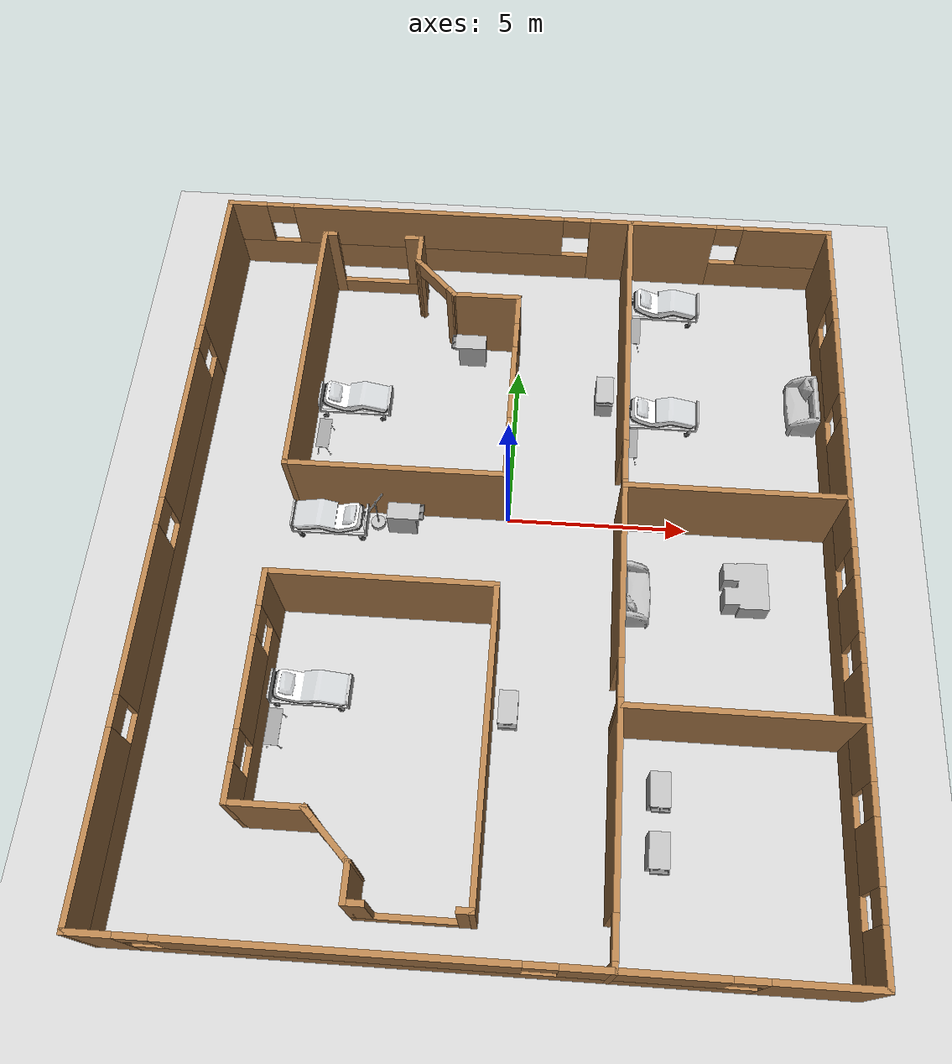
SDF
<sdf version="1.6">
 <world name="default">
  <model name="ground_plane">
   <static>1</static>
   <link name="link">
    <collision name="collision">
     <geometry><plane><normal>0 0 1</normal><size>100 100</size></plane></geometry>
     <surface>
      <contact><collide_bitmask>65535</collide_bitmask></contact>
      <friction><ode><mu>100</mu><mu2>50</mu2></ode></friction>
     </surface>
    </collision>
    <visual name="visual">
     <cast_shadows>0</cast_shadows>
     <geometry><plane><normal>0 0 1</normal><size>100 100</size></plane></geometry>
     <material>
      <script><uri>file://media/materials/scripts/gazebo.material</uri><name>Gazebo/Grey</name></script>
     </material>
    </visual>
   </link>
  </model>
  <gravity>0 0 -9.8</gravity>
  <magnetic_field>6e-06 2.3e-05 -4.2e-05</magnetic_field>
  <atmosphere type="adiabatic"/>
  <physics name="default_physics" default="0" type="ode">
   <max_step_size>0.001</max_step_size>
   <real_time_factor>1</real_time_factor>
   <real_time_update_rate>1000</real_time_update_rate>
  </physics>
  <scene><ambient>0.4 0.4 0.4 1</ambient><background>0.7 0.7 0.7 1</background><shadows>0</shadows></scene>
  <audio><device>default</device></audio>
  <spherical_coordinates>
   <surface_model>EARTH_WGS84</surface_model>
   <latitude_deg>0</latitude_deg>
   <longitude_deg>0</longitude_deg>
   <elevation>0</elevation>
   <heading_deg>0</heading_deg>
  </spherical_coordinates>
  <model name="hospital_room_empty">
   <link name="Wall_0">
    <pose>-4e-06 -3.9165 0 0 -0 0</pose>
    <visual name="Wall_0_Visual">
     <pose>0 0 1.25 0 -0 0</pose>
     <geometry><box><size>6 0.15 2.5</size></box></geometry>
     <material>
      <script><uri>file://media/materials/scripts/gazebo.material</uri><name>Gazebo/Wood</name></script>
      <ambient>1 1 1 1</ambient>
     </material>
     <meta><layer>0</layer></meta>
    </visual>
    <collision name="Wall_0_Collision">
     <pose>0 0 1.25 0 -0 0</pose>
     <geometry><box><size>6 0.15 2.5</size></box></geometry>
     <surface>
      <friction>
       <ode><mu>1</mu><mu2>1</mu2><fdir1>0 0 0</fdir1><slip1>0</slip1><slip2>0</slip2></ode>
       <torsional>
        <coefficient>1</coefficient>
        <patch_radius>0</patch_radius>
        <surface_radius>0</surface_radius>
        <use_patch_radius>1</use_patch_radius>
        <ode><slip>0</slip></ode>
       </torsional>
      </friction>
      <bounce><restitution_coefficient>0</restitution_coefficient><threshold>1e+06</threshold></bounce>
      <contact>
       <collide_without_contact>0</collide_without_contact>
       <collide_without_contact_bitmask>1</collide_without_contact_bitmask>
       <collide_bitmask>1</collide_bitmask>
       <ode>
        <soft_cfm>0</soft_cfm>
        <soft_erp>0.2</soft_erp>
        <kp>1e+13</kp>
        <kd>1</kd>
        <max_vel>0.01</max_vel>
        <min_depth>0</min_depth>
       </ode>
       <bullet>
        <split_impulse>1</split_impulse>
        <split_impulse_penetration_threshold>-0.01</split_impulse_penetration_threshold>
        <soft_cfm>0</soft_cfm>
        <soft_erp>0.2</soft_erp>
        <kp>1e+13</kp>
        <kd>1</kd>
       </bullet>
      </contact>
     </surface>
    </collision>
   </link>
   <link name="Wall_3">
    <pose>-2.925 0 0 0 -0 1.5708</pose>
    <visual name="Wall_3_Visual">
     <pose>0 0 1.25 0 -0 0</pose>
     <geometry><box><size>7.98302 0.15 2.5</size></box></geometry>
     <material>
      <script><uri>file://media/materials/scripts/gazebo.material</uri><name>Gazebo/Wood</name></script>
      <ambient>1 1 1 1</ambient>
     </material>
     <meta><layer>0</layer></meta>
    </visual>
    <collision name="Wall_3_Collision">
     <pose>0 0 1.25 0 -0 0</pose>
     <geometry><box><size>7.98302 0.15 2.5</size></box></geometry>
     <surface>
      <friction>
       <ode><mu>1</mu><mu2>1</mu2><fdir1>0 0 0</fdir1><slip1>0</slip1><slip2>0</slip2></ode>
       <torsional>
        <coefficient>1</coefficient>
        <patch_radius>0</patch_radius>
        <surface_radius>0</surface_radius>
        <use_patch_radius>1</use_patch_radius>
        <ode><slip>0</slip></ode>
       </torsional>
      </friction>
      <bounce><restitution_coefficient>0</restitution_coefficient><threshold>1e+06</threshold></bounce>
      <contact>
       <collide_without_contact>0</collide_without_contact>
       <collide_without_contact_bitmask>1</collide_without_contact_bitmask>
       <collide_bitmask>1</collide_bitmask>
       <ode>
        <soft_cfm>0</soft_cfm>
        <soft_erp>0.2</soft_erp>
        <kp>1e+13</kp>
        <kd>1</kd>
        <max_vel>0.01</max_vel>
        <min_depth>0</min_depth>
       </ode>
       <bullet>
        <split_impulse>1</split_impulse>
        <split_impulse_penetration_threshold>-0.01</split_impulse_penetration_threshold>
        <soft_cfm>0</soft_cfm>
        <soft_erp>0.2</soft_erp>
        <kp>1e+13</kp>
        <kd>1</kd>
       </bullet>
      </contact>
     </surface>
    </collision>
   </link>
   <link name="Wall_4">
    <pose>-1.5 3.9165 0 0 -0 0</pose>
    <visual name="Wall_4_Visual_0">
     <pose>-1.28125 0 1.25 0 -0 0</pose>
     <geometry><box><size>0.437506 0.15 2.5</size></box></geometry>
     <material>
      <script><uri>file://media/materials/scripts/gazebo.material</uri><name>Gazebo/Wood</name></script>
      <ambient>1 1 1 1</ambient>
     </material>
     <meta><layer>0</layer></meta>
    </visual>
    <visual name="Wall_4_Visual_1">
     <pose>0.218753 0 0.25 0 -0 0</pose>
     <geometry><box><size>2.56249 0.15 0.5</size></box></geometry>
     <material>
      <script><uri>file://media/materials/scripts/gazebo.material</uri><name>Gazebo/Wood</name></script>
      <ambient>1 1 1 1</ambient>
     </material>
     <meta><layer>0</layer></meta>
    </visual>
    <visual name="Wall_4_Visual_2">
     <pose>1.21875 0 1.5 0 -0 0</pose>
     <geometry><box><size>0.562494 0.15 2</size></box></geometry>
     <material>
      <script><uri>file://media/materials/scripts/gazebo.material</uri><name>Gazebo/Wood</name></script>
      <ambient>1 1 1 1</ambient>
     </material>
     <meta><layer>0</layer></meta>
    </visual>
    <collision name="Wall_4_Collision_0">
     <pose>-1.28125 0 1.25 0 -0 0</pose>
     <geometry><box><size>0.437506 0.15 2.5</size></box></geometry>
     <surface>
      <friction>
       <ode><mu>1</mu><mu2>1</mu2><fdir1>0 0 0</fdir1><slip1>0</slip1><slip2>0</slip2></ode>
       <torsional>
        <coefficient>1</coefficient>
        <patch_radius>0</patch_radius>
        <surface_radius>0</surface_radius>
        <use_patch_radius>1</use_patch_radius>
        <ode><slip>0</slip></ode>
       </torsional>
      </friction>
      <bounce><restitution_coefficient>0</restitution_coefficient><threshold>1e+06</threshold></bounce>
      <contact>
       <collide_without_contact>0</collide_without_contact>
       <collide_without_contact_bitmask>1</collide_without_contact_bitmask>
       <collide_bitmask>1</collide_bitmask>
       <ode>
        <soft_cfm>0</soft_cfm>
        <soft_erp>0.2</soft_erp>
        <kp>1e+13</kp>
        <kd>1</kd>
        <max_vel>0.01</max_vel>
        <min_depth>0</min_depth>
       </ode>
       <bullet>
        <split_impulse>1</split_impulse>
        <split_impulse_penetration_threshold>-0.01</split_impulse_penetration_threshold>
        <soft_cfm>0</soft_cfm>
        <soft_erp>0.2</soft_erp>
        <kp>1e+13</kp>
        <kd>1</kd>
       </bullet>
      </contact>
     </surface>
    </collision>
    <collision name="Wall_4_Collision_1">
     <pose>0.218753 0 0.25 0 -0 0</pose>
     <geometry><box><size>2.56249 0.15 0.5</size></box></geometry>
     <surface>
      <friction>
       <ode><mu>1</mu><mu2>1</mu2><fdir1>0 0 0</fdir1><slip1>0</slip1><slip2>0</slip2></ode>
       <torsional>
        <coefficient>1</coefficient>
        <patch_radius>0</patch_radius>
        <surface_radius>0</surface_radius>
        <use_patch_radius>1</use_patch_radius>
        <ode><slip>0</slip></ode>
       </torsional>
      </friction>
      <bounce><restitution_coefficient>0</restitution_coefficient><threshold>1e+06</threshold></bounce>
      <contact>
       <collide_without_contact>0</collide_without_contact>
       <collide_without_contact_bitmask>1</collide_without_contact_bitmask>
       <collide_bitmask>1</collide_bitmask>
       <ode>
        <soft_cfm>0</soft_cfm>
        <soft_erp>0.2</soft_erp>
        <kp>1e+13</kp>
        <kd>1</kd>
        <max_vel>0.01</max_vel>
        <min_depth>0</min_depth>
       </ode>
       <bullet>
        <split_impulse>1</split_impulse>
        <split_impulse_penetration_threshold>-0.01</split_impulse_penetration_threshold>
        <soft_cfm>0</soft_cfm>
        <soft_erp>0.2</soft_erp>
        <kp>1e+13</kp>
        <kd>1</kd>
       </bullet>
      </contact>
     </surface>
    </collision>
    <collision name="Wall_4_Collision_2">
     <pose>1.21875 0 1.5 0 -0 0</pose>
     <geometry><box><size>0.562494 0.15 2</size></box></geometry>
     <surface>
      <friction>
       <ode><mu>1</mu><mu2>1</mu2><fdir1>0 0 0</fdir1><slip1>0</slip1><slip2>0</slip2></ode>
       <torsional>
        <coefficient>1</coefficient>
        <patch_radius>0</patch_radius>
        <surface_radius>0</surface_radius>
        <use_patch_radius>1</use_patch_radius>
        <ode><slip>0</slip></ode>
       </torsional>
      </friction>
      <bounce><restitution_coefficient>0</restitution_coefficient><threshold>1e+06</threshold></bounce>
      <contact>
       <collide_without_contact>0</collide_without_contact>
       <collide_without_contact_bitmask>1</collide_without_contact_bitmask>
       <collide_bitmask>1</collide_bitmask>
       <ode>
        <soft_cfm>0</soft_cfm>
        <soft_erp>0.2</soft_erp>
        <kp>1e+13</kp>
        <kd>1</kd>
        <max_vel>0.01</max_vel>
        <min_depth>0</min_depth>
       </ode>
       <bullet>
        <split_impulse>1</split_impulse>
        <split_impulse_penetration_threshold>-0.01</split_impulse_penetration_threshold>
        <soft_cfm>0</soft_cfm>
        <soft_erp>0.2</soft_erp>
        <kp>1e+13</kp>
        <kd>1</kd>
       </bullet>
      </contact>
     </surface>
    </collision>
   </link>
   <link name="Wall_5">
    <pose>-0.075004 3.4915 0 0 0 -1.5708</pose>
    <visual name="Wall_5_Visual">
     <pose>0 0 1.25 0 -0 0</pose>
     <geometry><box><size>1 0.15 2.5</size></box></geometry>
     <material>
      <script><uri>file://media/materials/scripts/gazebo.material</uri><name>Gazebo/Wood</name></script>
      <ambient>1 1 1 1</ambient>
     </material>
     <meta><layer>0</layer></meta>
    </visual>
    <collision name="Wall_5_Collision">
     <pose>0 0 1.25 0 -0 0</pose>
     <geometry><box><size>1 0.15 2.5</size></box></geometry>
     <surface>
      <friction>
       <ode><mu>1</mu><mu2>1</mu2><fdir1>0 0 0</fdir1><slip1>0</slip1><slip2>0</slip2></ode>
       <torsional>
        <coefficient>1</coefficient>
        <patch_radius>0</patch_radius>
        <surface_radius>0</surface_radius>
        <use_patch_radius>1</use_patch_radius>
        <ode><slip>0</slip></ode>
       </torsional>
      </friction>
      <bounce><restitution_coefficient>0</restitution_coefficient><threshold>1e+06</threshold></bounce>
      <contact>
       <collide_without_contact>0</collide_without_contact>
       <collide_without_contact_bitmask>1</collide_without_contact_bitmask>
       <collide_bitmask>1</collide_bitmask>
       <ode>
        <soft_cfm>0</soft_cfm>
        <soft_erp>0.2</soft_erp>
        <kp>1e+13</kp>
        <kd>1</kd>
        <max_vel>0.01</max_vel>
        <min_depth>0</min_depth>
       </ode>
       <bullet>
        <split_impulse>1</split_impulse>
        <split_impulse_penetration_threshold>-0.01</split_impulse_penetration_threshold>
        <soft_cfm>0</soft_cfm>
        <soft_erp>0.2</soft_erp>
        <kp>1e+13</kp>
        <kd>1</kd>
       </bullet>
      </contact>
     </surface>
    </collision>
   </link>
   <link name="Wall_7">
    <pose>2.925 -1 0 0 -0 1.5708</pose>
    <visual name="Wall_7_Visual_0">
     <pose>-2.47597 0 1.25 0 -0 0</pose>
     <geometry><box><size>1.03106 0.15 2.5</size></box></geometry>
     <material>
      <script><uri>file://media/materials/scripts/gazebo.material</uri><name>Gazebo/Wood</name></script>
      <ambient>0.921569 0.807843 0.615686 1</ambient>
     </material>
     <meta><layer>0</layer></meta>
    </visual>
    <visual name="Wall_7_Visual_1">
     <pose>0.515531 0 0.5 0 -0 0</pose>
     <geometry><box><size>4.95194 0.15 1</size></box></geometry>
     <material>
      <script><uri>file://media/materials/scripts/gazebo.material</uri><name>Gazebo/Wood</name></script>
      <ambient>0.921569 0.807843 0.615686 1</ambient>
     </material>
     <meta><layer>0</layer></meta>
    </visual>
    <visual name="Wall_7_Visual_2">
     <pose>0.016139 0 1.75 0 -0 0</pose>
     <geometry><box><size>2.35315 0.15 1.5</size></box></geometry>
     <material>
      <script><uri>file://media/materials/scripts/gazebo.material</uri><name>Gazebo/Wood</name></script>
      <ambient>0.921569 0.807843 0.615686 1</ambient>
     </material>
     <meta><layer>0</layer></meta>
    </visual>
    <visual name="Wall_7_Visual_3">
     <pose>2.49211 0 1.75 0 -0 0</pose>
     <geometry><box><size>0.998785 0.15 1.5</size></box></geometry>
     <material>
      <script><uri>file://media/materials/scripts/gazebo.material</uri><name>Gazebo/Wood</name></script>
      <ambient>0.921569 0.807843 0.615686 1</ambient>
     </material>
     <meta><layer>0</layer></meta>
    </visual>
    <visual name="Wall_7_Visual_4">
     <pose>-1.56044 0 2.15 0 -0 0</pose>
     <geometry><box><size>0.8 0.15 0.7</size></box></geometry>
     <material>
      <script><uri>file://media/materials/scripts/gazebo.material</uri><name>Gazebo/Wood</name></script>
      <ambient>0.921569 0.807843 0.615686 1</ambient>
     </material>
     <meta><layer>0</layer></meta>
    </visual>
    <visual name="Wall_7_Visual_5">
     <pose>1.59272 0 2.15 0 -0 0</pose>
     <geometry><box><size>0.8 0.15 0.7</size></box></geometry>
     <material>
      <script><uri>file://media/materials/scripts/gazebo.material</uri><name>Gazebo/Wood</name></script>
      <ambient>0.921569 0.807843 0.615686 1</ambient>
     </material>
     <meta><layer>0</layer></meta>
    </visual>
    <collision name="Wall_7_Collision_0">
     <pose>-2.47597 0 1.25 0 -0 0</pose>
     <geometry><box><size>1.03106 0.15 2.5</size></box></geometry>
     <surface>
      <friction>
       <ode><mu>1</mu><mu2>1</mu2><fdir1>0 0 0</fdir1><slip1>0</slip1><slip2>0</slip2></ode>
       <torsional>
        <coefficient>1</coefficient>
        <patch_radius>0</patch_radius>
        <surface_radius>0</surface_radius>
        <use_patch_radius>1</use_patch_radius>
        <ode><slip>0</slip></ode>
       </torsional>
      </friction>
      <bounce><restitution_coefficient>0</restitution_coefficient><threshold>1e+06</threshold></bounce>
      <contact>
       <collide_without_contact>0</collide_without_contact>
       <collide_without_contact_bitmask>1</collide_without_contact_bitmask>
       <collide_bitmask>1</collide_bitmask>
       <ode>
        <soft_cfm>0</soft_cfm>
        <soft_erp>0.2</soft_erp>
        <kp>1e+13</kp>
        <kd>1</kd>
        <max_vel>0.01</max_vel>
        <min_depth>0</min_depth>
       </ode>
       <bullet>
        <split_impulse>1</split_impulse>
        <split_impulse_penetration_threshold>-0.01</split_impulse_penetration_threshold>
        <soft_cfm>0</soft_cfm>
        <soft_erp>0.2</soft_erp>
        <kp>1e+13</kp>
        <kd>1</kd>
       </bullet>
      </contact>
     </surface>
    </collision>
    <collision name="Wall_7_Collision_1">
     <pose>0.515531 0 0.5 0 -0 0</pose>
     <geometry><box><size>4.95194 0.15 1</size></box></geometry>
     <surface>
      <friction>
       <ode><mu>1</mu><mu2>1</mu2><fdir1>0 0 0</fdir1><slip1>0</slip1><slip2>0</slip2></ode>
       <torsional>
        <coefficient>1</coefficient>
        <patch_radius>0</patch_radius>
        <surface_radius>0</surface_radius>
        <use_patch_radius>1</use_patch_radius>
        <ode><slip>0</slip></ode>
       </torsional>
      </friction>
      <bounce><restitution_coefficient>0</restitution_coefficient><threshold>1e+06</threshold></bounce>
      <contact>
       <collide_without_contact>0</collide_without_contact>
       <collide_without_contact_bitmask>1</collide_without_contact_bitmask>
       <collide_bitmask>1</collide_bitmask>
       <ode>
        <soft_cfm>0</soft_cfm>
        <soft_erp>0.2</soft_erp>
        <kp>1e+13</kp>
        <kd>1</kd>
        <max_vel>0.01</max_vel>
        <min_depth>0</min_depth>
       </ode>
       <bullet>
        <split_impulse>1</split_impulse>
        <split_impulse_penetration_threshold>-0.01</split_impulse_penetration_threshold>
        <soft_cfm>0</soft_cfm>
        <soft_erp>0.2</soft_erp>
        <kp>1e+13</kp>
        <kd>1</kd>
       </bullet>
      </contact>
     </surface>
    </collision>
    <collision name="Wall_7_Collision_2">
     <pose>0.016139 0 1.75 0 -0 0</pose>
     <geometry><box><size>2.35315 0.15 1.5</size></box></geometry>
     <surface>
      <friction>
       <ode><mu>1</mu><mu2>1</mu2><fdir1>0 0 0</fdir1><slip1>0</slip1><slip2>0</slip2></ode>
       <torsional>
        <coefficient>1</coefficient>
        <patch_radius>0</patch_radius>
        <surface_radius>0</surface_radius>
        <use_patch_radius>1</use_patch_radius>
        <ode><slip>0</slip></ode>
       </torsional>
      </friction>
      <bounce><restitution_coefficient>0</restitution_coefficient><threshold>1e+06</threshold></bounce>
      <contact>
       <collide_without_contact>0</collide_without_contact>
       <collide_without_contact_bitmask>1</collide_without_contact_bitmask>
       <collide_bitmask>1</collide_bitmask>
       <ode>
        <soft_cfm>0</soft_cfm>
        <soft_erp>0.2</soft_erp>
        <kp>1e+13</kp>
        <kd>1</kd>
        <max_vel>0.01</max_vel>
        <min_depth>0</min_depth>
       </ode>
       <bullet>
        <split_impulse>1</split_impulse>
        <split_impulse_penetration_threshold>-0.01</split_impulse_penetration_threshold>
        <soft_cfm>0</soft_cfm>
        <soft_erp>0.2</soft_erp>
        <kp>1e+13</kp>
        <kd>1</kd>
       </bullet>
      </contact>
     </surface>
    </collision>
    <collision name="Wall_7_Collision_3">
     <pose>2.49211 0 1.75 0 -0 0</pose>
     <geometry><box><size>0.998785 0.15 1.5</size></box></geometry>
     <surface>
      <friction>
       <ode><mu>1</mu><mu2>1</mu2><fdir1>0 0 0</fdir1><slip1>0</slip1><slip2>0</slip2></ode>
       <torsional>
        <coefficient>1</coefficient>
        <patch_radius>0</patch_radius>
        <surface_radius>0</surface_radius>
        <use_patch_radius>1</use_patch_radius>
        <ode><slip>0</slip></ode>
       </torsional>
      </friction>
      <bounce><restitution_coefficient>0</restitution_coefficient><threshold>1e+06</threshold></bounce>
      <contact>
       <collide_without_contact>0</collide_without_contact>
       <collide_without_contact_bitmask>1</collide_without_contact_bitmask>
       <collide_bitmask>1</collide_bitmask>
       <ode>
        <soft_cfm>0</soft_cfm>
        <soft_erp>0.2</soft_erp>
        <kp>1e+13</kp>
        <kd>1</kd>
        <max_vel>0.01</max_vel>
        <min_depth>0</min_depth>
       </ode>
       <bullet>
        <split_impulse>1</split_impulse>
        <split_impulse_penetration_threshold>-0.01</split_impulse_penetration_threshold>
        <soft_cfm>0</soft_cfm>
        <soft_erp>0.2</soft_erp>
        <kp>1e+13</kp>
        <kd>1</kd>
       </bullet>
      </contact>
     </surface>
    </collision>
    <collision name="Wall_7_Collision_4">
     <pose>-1.56044 0 2.15 0 -0 0</pose>
     <geometry><box><size>0.8 0.15 0.7</size></box></geometry>
     <surface>
      <friction>
       <ode><mu>1</mu><mu2>1</mu2><fdir1>0 0 0</fdir1><slip1>0</slip1><slip2>0</slip2></ode>
       <torsional>
        <coefficient>1</coefficient>
        <patch_radius>0</patch_radius>
        <surface_radius>0</surface_radius>
        <use_patch_radius>1</use_patch_radius>
        <ode><slip>0</slip></ode>
       </torsional>
      </friction>
      <bounce><restitution_coefficient>0</restitution_coefficient><threshold>1e+06</threshold></bounce>
      <contact>
       <collide_without_contact>0</collide_without_contact>
       <collide_without_contact_bitmask>1</collide_without_contact_bitmask>
       <collide_bitmask>1</collide_bitmask>
       <ode>
        <soft_cfm>0</soft_cfm>
        <soft_erp>0.2</soft_erp>
        <kp>1e+13</kp>
        <kd>1</kd>
        <max_vel>0.01</max_vel>
        <min_depth>0</min_depth>
       </ode>
       <bullet>
        <split_impulse>1</split_impulse>
        <split_impulse_penetration_threshold>-0.01</split_impulse_penetration_threshold>
        <soft_cfm>0</soft_cfm>
        <soft_erp>0.2</soft_erp>
        <kp>1e+13</kp>
        <kd>1</kd>
       </bullet>
      </contact>
     </surface>
    </collision>
    <collision name="Wall_7_Collision_5">
     <pose>1.59272 0 2.15 0 -0 0</pose>
     <geometry><box><size>0.8 0.15 0.7</size></box></geometry>
     <surface>
      <friction>
       <ode><mu>1</mu><mu2>1</mu2><fdir1>0 0 0</fdir1><slip1>0</slip1><slip2>0</slip2></ode>
       <torsional>
        <coefficient>1</coefficient>
        <patch_radius>0</patch_radius>
        <surface_radius>0</surface_radius>
        <use_patch_radius>1</use_patch_radius>
        <ode><slip>0</slip></ode>
       </torsional>
      </friction>
      <bounce><restitution_coefficient>0</restitution_coefficient><threshold>1e+06</threshold></bounce>
      <contact>
       <collide_without_contact>0</collide_without_contact>
       <collide_without_contact_bitmask>1</collide_without_contact_bitmask>
       <collide_bitmask>1</collide_bitmask>
       <ode>
        <soft_cfm>0</soft_cfm>
        <soft_erp>0.2</soft_erp>
        <kp>1e+13</kp>
        <kd>1</kd>
        <max_vel>0.01</max_vel>
        <min_depth>0</min_depth>
       </ode>
       <bullet>
        <split_impulse>1</split_impulse>
        <split_impulse_penetration_threshold>-0.01</split_impulse_penetration_threshold>
        <soft_cfm>0</soft_cfm>
        <soft_erp>0.2</soft_erp>
        <kp>1e+13</kp>
        <kd>1</kd>
       </bullet>
      </contact>
     </surface>
    </collision>
   </link>
   <link name="Wall_8">
    <pose>2 1.9166 0 0 -0 3.14148</pose>
    <visual name="Wall_8_Visual">
     <pose>0 0 1.25 0 -0 0</pose>
     <geometry><box><size>2 0.15 2.5</size></box></geometry>
     <material>
      <script><uri>file://media/materials/scripts/gazebo.material</uri><name>Gazebo/Wood</name></script>
      <ambient>1 1 1 1</ambient>
     </material>
     <meta><layer>0</layer></meta>
    </visual>
    <collision name="Wall_8_Collision">
     <pose>0 0 1.25 0 -0 0</pose>
     <geometry><box><size>2 0.15 2.5</size></box></geometry>
     <surface>
      <friction>
       <ode><mu>1</mu><mu2>1</mu2><fdir1>0 0 0</fdir1><slip1>0</slip1><slip2>0</slip2></ode>
       <torsional>
        <coefficient>1</coefficient>
        <patch_radius>0</patch_radius>
        <surface_radius>0</surface_radius>
        <use_patch_radius>1</use_patch_radius>
        <ode><slip>0</slip></ode>
       </torsional>
      </friction>
      <bounce><restitution_coefficient>0</restitution_coefficient><threshold>1e+06</threshold></bounce>
      <contact>
       <collide_without_contact>0</collide_without_contact>
       <collide_without_contact_bitmask>1</collide_without_contact_bitmask>
       <collide_bitmask>1</collide_bitmask>
       <ode>
        <soft_cfm>0</soft_cfm>
        <soft_erp>0.2</soft_erp>
        <kp>1e+13</kp>
        <kd>1</kd>
        <max_vel>0.01</max_vel>
        <min_depth>0</min_depth>
       </ode>
       <bullet>
        <split_impulse>1</split_impulse>
        <split_impulse_penetration_threshold>-0.01</split_impulse_penetration_threshold>
        <soft_cfm>0</soft_cfm>
        <soft_erp>0.2</soft_erp>
        <kp>1e+13</kp>
        <kd>1</kd>
       </bullet>
      </contact>
     </surface>
    </collision>
   </link>
   <link name="Wall_9">
    <pose>0.499996 2.4916 0 0 -0 2.35628</pose>
    <visual name="Wall_9_Visual_1">
     <pose>0.785148 0 1.25 0 -0 0</pose>
     <geometry><box><size>0.205905 0.15 2.5</size></box></geometry>
     <material>
      <script><uri>file://media/materials/scripts/gazebo.material</uri><name>Gazebo/Wood</name></script>
      <ambient>1 1 1 1</ambient>
     </material>
     <meta><layer>0</layer></meta>
    </visual>
    <visual name="Wall_9_Visual_0">
     <pose>-0.702952 0 1.25 0 -0 0</pose>
     <geometry><box><size>0.370295 0.15 2.5</size></box></geometry>
     <material>
      <script><uri>file://media/materials/scripts/gazebo.material</uri><name>Gazebo/Wood</name></script>
      <ambient>1 1 1 1</ambient>
     </material>
     <meta><layer>0</layer></meta>
    </visual>
    <visual name="Wall_9_Visual_2">
     <pose>0.082195 0 2.25 0 -0 0</pose>
     <geometry><box><size>1.2 0.15 0.5</size></box></geometry>
     <material>
      <script><uri>file://media/materials/scripts/gazebo.material</uri><name>Gazebo/Wood</name></script>
      <ambient>1 1 1 1</ambient>
     </material>
     <meta><layer>0</layer></meta>
    </visual>
    <collision name="Wall_9_Collision_0">
     <pose>-0.702952 0 1.25 0 -0 0</pose>
     <geometry><box><size>0.370295 0.15 2.5</size></box></geometry>
     <surface>
      <friction>
       <ode><mu>1</mu><mu2>1</mu2><fdir1>0 0 0</fdir1><slip1>0</slip1><slip2>0</slip2></ode>
       <torsional>
        <coefficient>1</coefficient>
        <patch_radius>0</patch_radius>
        <surface_radius>0</surface_radius>
        <use_patch_radius>1</use_patch_radius>
        <ode><slip>0</slip></ode>
       </torsional>
      </friction>
      <bounce><restitution_coefficient>0</restitution_coefficient><threshold>1e+06</threshold></bounce>
      <contact>
       <collide_without_contact>0</collide_without_contact>
       <collide_without_contact_bitmask>1</collide_without_contact_bitmask>
       <collide_bitmask>1</collide_bitmask>
       <ode>
        <soft_cfm>0</soft_cfm>
        <soft_erp>0.2</soft_erp>
        <kp>1e+13</kp>
        <kd>1</kd>
        <max_vel>0.01</max_vel>
        <min_depth>0</min_depth>
       </ode>
       <bullet>
        <split_impulse>1</split_impulse>
        <split_impulse_penetration_threshold>-0.01</split_impulse_penetration_threshold>
        <soft_cfm>0</soft_cfm>
        <soft_erp>0.2</soft_erp>
        <kp>1e+13</kp>
        <kd>1</kd>
       </bullet>
      </contact>
     </surface>
    </collision>
    <collision name="Wall_9_Collision_1">
     <pose>0.785148 0 1.25 0 -0 0</pose>
     <geometry><box><size>0.205905 0.15 2.5</size></box></geometry>
     <surface>
      <friction>
       <ode><mu>1</mu><mu2>1</mu2><fdir1>0 0 0</fdir1><slip1>0</slip1><slip2>0</slip2></ode>
       <torsional>
        <coefficient>1</coefficient>
        <patch_radius>0</patch_radius>
        <surface_radius>0</surface_radius>
        <use_patch_radius>1</use_patch_radius>
        <ode><slip>0</slip></ode>
       </torsional>
      </friction>
      <bounce><restitution_coefficient>0</restitution_coefficient><threshold>1e+06</threshold></bounce>
      <contact>
       <collide_without_contact>0</collide_without_contact>
       <collide_without_contact_bitmask>1</collide_without_contact_bitmask>
       <collide_bitmask>1</collide_bitmask>
       <ode>
        <soft_cfm>0</soft_cfm>
        <soft_erp>0.2</soft_erp>
        <kp>1e+13</kp>
        <kd>1</kd>
        <max_vel>0.01</max_vel>
        <min_depth>0</min_depth>
       </ode>
       <bullet>
        <split_impulse>1</split_impulse>
        <split_impulse_penetration_threshold>-0.01</split_impulse_penetration_threshold>
        <soft_cfm>0</soft_cfm>
        <soft_erp>0.2</soft_erp>
        <kp>1e+13</kp>
        <kd>1</kd>
       </bullet>
      </contact>
     </surface>
    </collision>
    <collision name="Wall_9_Collision_2">
     <pose>0.082195 0 2.25 0 -0 0</pose>
     <geometry><box><size>1.2 0.15 0.5</size></box></geometry>
     <surface>
      <friction>
       <ode><mu>1</mu><mu2>1</mu2><fdir1>0 0 0</fdir1><slip1>0</slip1><slip2>0</slip2></ode>
       <torsional>
        <coefficient>1</coefficient>
        <patch_radius>0</patch_radius>
        <surface_radius>0</surface_radius>
        <use_patch_radius>1</use_patch_radius>
        <ode><slip>0</slip></ode>
       </torsional>
      </friction>
      <bounce><restitution_coefficient>0</restitution_coefficient><threshold>1e+06</threshold></bounce>
      <contact>
       <collide_without_contact>0</collide_without_contact>
       <collide_without_contact_bitmask>1</collide_without_contact_bitmask>
       <collide_bitmask>1</collide_bitmask>
       <ode>
        <soft_cfm>0</soft_cfm>
        <soft_erp>0.2</soft_erp>
        <kp>1e+13</kp>
        <kd>1</kd>
        <max_vel>0.01</max_vel>
        <min_depth>0</min_depth>
       </ode>
       <bullet>
        <split_impulse>1</split_impulse>
        <split_impulse_penetration_threshold>-0.01</split_impulse_penetration_threshold>
        <soft_cfm>0</soft_cfm>
        <soft_erp>0.2</soft_erp>
        <kp>1e+13</kp>
        <kd>1</kd>
       </bullet>
      </contact>
     </surface>
    </collision>
   </link>
   <static>1</static>
   <pose>-3.00848 4.0001 0 0 -0 0</pose>
  </model>
  <model name="hospital_room_empty_clone">
   <link name="Wall_0">
    <pose>-4e-06 -3.9165 0 0 -0 0</pose>
    <visual name="Wall_0_Visual">
     <pose>0 0 1.25 0 -0 0</pose>
     <geometry><box><size>6 0.15 2.5</size></box></geometry>
     <material>
      <script><uri>file://media/materials/scripts/gazebo.material</uri><name>Gazebo/Wood</name></script>
      <ambient>1 1 1 1</ambient>
     </material>
     <meta><layer>0</layer></meta>
    </visual>
    <collision name="Wall_0_Collision">
     <pose>0 0 1.25 0 -0 0</pose>
     <geometry><box><size>6 0.15 2.5</size></box></geometry>
     <surface>
      <friction>
       <ode><mu>1</mu><mu2>1</mu2><fdir1>0 0 0</fdir1><slip1>0</slip1><slip2>0</slip2></ode>
       <torsional>
        <coefficient>1</coefficient>
        <patch_radius>0</patch_radius>
        <surface_radius>0</surface_radius>
        <use_patch_radius>1</use_patch_radius>
        <ode><slip>0</slip></ode>
       </torsional>
      </friction>
      <bounce><restitution_coefficient>0</restitution_coefficient><threshold>1e+06</threshold></bounce>
      <contact>
       <collide_without_contact>0</collide_without_contact>
       <collide_without_contact_bitmask>1</collide_without_contact_bitmask>
       <collide_bitmask>1</collide_bitmask>
       <ode>
        <soft_cfm>0</soft_cfm>
        <soft_erp>0.2</soft_erp>
        <kp>1e+13</kp>
        <kd>1</kd>
        <max_vel>0.01</max_vel>
        <min_depth>0</min_depth>
       </ode>
       <bullet>
        <split_impulse>1</split_impulse>
        <split_impulse_penetration_threshold>-0.01</split_impulse_penetration_threshold>
        <soft_cfm>0</soft_cfm>
        <soft_erp>0.2</soft_erp>
        <kp>1e+13</kp>
        <kd>1</kd>
       </bullet>
      </contact>
     </surface>
    </collision>
   </link>
   <link name="Wall_3">
    <pose>-2.925 0 0 0 -0 1.5708</pose>
    <visual name="Wall_3_Visual">
     <pose>0 0 1.25 0 -0 0</pose>
     <geometry><box><size>7.98302 0.15 2.5</size></box></geometry>
     <material>
      <script><uri>file://media/materials/scripts/gazebo.material</uri><name>Gazebo/Wood</name></script>
      <ambient>1 1 1 1</ambient>
     </material>
     <meta><layer>0</layer></meta>
    </visual>
    <collision name="Wall_3_Collision">
     <pose>0 0 1.25 0 -0 0</pose>
     <geometry><box><size>7.98302 0.15 2.5</size></box></geometry>
     <surface>
      <friction>
       <ode><mu>1</mu><mu2>1</mu2><fdir1>0 0 0</fdir1><slip1>0</slip1><slip2>0</slip2></ode>
       <torsional>
        <coefficient>1</coefficient>
        <patch_radius>0</patch_radius>
        <surface_radius>0</surface_radius>
        <use_patch_radius>1</use_patch_radius>
        <ode><slip>0</slip></ode>
       </torsional>
      </friction>
      <bounce><restitution_coefficient>0</restitution_coefficient><threshold>1e+06</threshold></bounce>
      <contact>
       <collide_without_contact>0</collide_without_contact>
       <collide_without_contact_bitmask>1</collide_without_contact_bitmask>
       <collide_bitmask>1</collide_bitmask>
       <ode>
        <soft_cfm>0</soft_cfm>
        <soft_erp>0.2</soft_erp>
        <kp>1e+13</kp>
        <kd>1</kd>
        <max_vel>0.01</max_vel>
        <min_depth>0</min_depth>
       </ode>
       <bullet>
        <split_impulse>1</split_impulse>
        <split_impulse_penetration_threshold>-0.01</split_impulse_penetration_threshold>
        <soft_cfm>0</soft_cfm>
        <soft_erp>0.2</soft_erp>
        <kp>1e+13</kp>
        <kd>1</kd>
       </bullet>
      </contact>
     </surface>
    </collision>
   </link>
   <link name="Wall_4">
    <pose>-1.5 3.9165 0 0 -0 0</pose>
    <visual name="Wall_4_Visual_0">
     <pose>-1.28125 0 1.25 0 -0 0</pose>
     <geometry><box><size>0.437506 0.15 2.5</size></box></geometry>
     <material>
      <script><uri>file://media/materials/scripts/gazebo.material</uri><name>Gazebo/Wood</name></script>
      <ambient>1 1 1 1</ambient>
     </material>
     <meta><layer>0</layer></meta>
    </visual>
    <visual name="Wall_4_Visual_1">
     <pose>0.218753 0 0.25 0 -0 0</pose>
     <geometry><box><size>2.56249 0.15 0.5</size></box></geometry>
     <material>
      <script><uri>file://media/materials/scripts/gazebo.material</uri><name>Gazebo/Wood</name></script>
      <ambient>1 1 1 1</ambient>
     </material>
     <meta><layer>0</layer></meta>
    </visual>
    <visual name="Wall_4_Visual_2">
     <pose>1.21875 0 1.5 0 -0 0</pose>
     <geometry><box><size>0.562494 0.15 2</size></box></geometry>
     <material>
      <script><uri>file://media/materials/scripts/gazebo.material</uri><name>Gazebo/Wood</name></script>
      <ambient>1 1 1 1</ambient>
     </material>
     <meta><layer>0</layer></meta>
    </visual>
    <collision name="Wall_4_Collision_0">
     <pose>-1.28125 0 1.25 0 -0 0</pose>
     <geometry><box><size>0.437506 0.15 2.5</size></box></geometry>
     <surface>
      <friction>
       <ode><mu>1</mu><mu2>1</mu2><fdir1>0 0 0</fdir1><slip1>0</slip1><slip2>0</slip2></ode>
       <torsional>
        <coefficient>1</coefficient>
        <patch_radius>0</patch_radius>
        <surface_radius>0</surface_radius>
        <use_patch_radius>1</use_patch_radius>
        <ode><slip>0</slip></ode>
       </torsional>
      </friction>
      <bounce><restitution_coefficient>0</restitution_coefficient><threshold>1e+06</threshold></bounce>
      <contact>
       <collide_without_contact>0</collide_without_contact>
       <collide_without_contact_bitmask>1</collide_without_contact_bitmask>
       <collide_bitmask>1</collide_bitmask>
       <ode>
        <soft_cfm>0</soft_cfm>
        <soft_erp>0.2</soft_erp>
        <kp>1e+13</kp>
        <kd>1</kd>
        <max_vel>0.01</max_vel>
        <min_depth>0</min_depth>
       </ode>
       <bullet>
        <split_impulse>1</split_impulse>
        <split_impulse_penetration_threshold>-0.01</split_impulse_penetration_threshold>
        <soft_cfm>0</soft_cfm>
        <soft_erp>0.2</soft_erp>
        <kp>1e+13</kp>
        <kd>1</kd>
       </bullet>
      </contact>
     </surface>
    </collision>
    <collision name="Wall_4_Collision_1">
     <pose>0.218753 0 0.25 0 -0 0</pose>
     <geometry><box><size>2.56249 0.15 0.5</size></box></geometry>
     <surface>
      <friction>
       <ode><mu>1</mu><mu2>1</mu2><fdir1>0 0 0</fdir1><slip1>0</slip1><slip2>0</slip2></ode>
       <torsional>
        <coefficient>1</coefficient>
        <patch_radius>0</patch_radius>
        <surface_radius>0</surface_radius>
        <use_patch_radius>1</use_patch_radius>
        <ode><slip>0</slip></ode>
       </torsional>
      </friction>
      <bounce><restitution_coefficient>0</restitution_coefficient><threshold>1e+06</threshold></bounce>
      <contact>
       <collide_without_contact>0</collide_without_contact>
       <collide_without_contact_bitmask>1</collide_without_contact_bitmask>
       <collide_bitmask>1</collide_bitmask>
       <ode>
        <soft_cfm>0</soft_cfm>
        <soft_erp>0.2</soft_erp>
        <kp>1e+13</kp>
        <kd>1</kd>
        <max_vel>0.01</max_vel>
        <min_depth>0</min_depth>
       </ode>
       <bullet>
        <split_impulse>1</split_impulse>
        <split_impulse_penetration_threshold>-0.01</split_impulse_penetration_threshold>
        <soft_cfm>0</soft_cfm>
        <soft_erp>0.2</soft_erp>
        <kp>1e+13</kp>
        <kd>1</kd>
       </bullet>
      </contact>
     </surface>
    </collision>
    <collision name="Wall_4_Collision_2">
     <pose>1.21875 0 1.5 0 -0 0</pose>
     <geometry><box><size>0.562494 0.15 2</size></box></geometry>
     <surface>
      <friction>
       <ode><mu>1</mu><mu2>1</mu2><fdir1>0 0 0</fdir1><slip1>0</slip1><slip2>0</slip2></ode>
       <torsional>
        <coefficient>1</coefficient>
        <patch_radius>0</patch_radius>
        <surface_radius>0</surface_radius>
        <use_patch_radius>1</use_patch_radius>
        <ode><slip>0</slip></ode>
       </torsional>
      </friction>
      <bounce><restitution_coefficient>0</restitution_coefficient><threshold>1e+06</threshold></bounce>
      <contact>
       <collide_without_contact>0</collide_without_contact>
       <collide_without_contact_bitmask>1</collide_without_contact_bitmask>
       <collide_bitmask>1</collide_bitmask>
       <ode>
        <soft_cfm>0</soft_cfm>
        <soft_erp>0.2</soft_erp>
        <kp>1e+13</kp>
        <kd>1</kd>
        <max_vel>0.01</max_vel>
        <min_depth>0</min_depth>
       </ode>
       <bullet>
        <split_impulse>1</split_impulse>
        <split_impulse_penetration_threshold>-0.01</split_impulse_penetration_threshold>
        <soft_cfm>0</soft_cfm>
        <soft_erp>0.2</soft_erp>
        <kp>1e+13</kp>
        <kd>1</kd>
       </bullet>
      </contact>
     </surface>
    </collision>
   </link>
   <link name="Wall_5">
    <pose>-0.075004 3.4915 0 0 0 -1.5708</pose>
    <visual name="Wall_5_Visual">
     <pose>0 0 1.25 0 -0 0</pose>
     <geometry><box><size>1 0.15 2.5</size></box></geometry>
     <material>
      <script><uri>file://media/materials/scripts/gazebo.material</uri><name>Gazebo/Wood</name></script>
      <ambient>1 1 1 1</ambient>
     </material>
     <meta><layer>0</layer></meta>
    </visual>
    <collision name="Wall_5_Collision">
     <pose>0 0 1.25 0 -0 0</pose>
     <geometry><box><size>1 0.15 2.5</size></box></geometry>
     <surface>
      <friction>
       <ode><mu>1</mu><mu2>1</mu2><fdir1>0 0 0</fdir1><slip1>0</slip1><slip2>0</slip2></ode>
       <torsional>
        <coefficient>1</coefficient>
        <patch_radius>0</patch_radius>
        <surface_radius>0</surface_radius>
        <use_patch_radius>1</use_patch_radius>
        <ode><slip>0</slip></ode>
       </torsional>
      </friction>
      <bounce><restitution_coefficient>0</restitution_coefficient><threshold>1e+06</threshold></bounce>
      <contact>
       <collide_without_contact>0</collide_without_contact>
       <collide_without_contact_bitmask>1</collide_without_contact_bitmask>
       <collide_bitmask>1</collide_bitmask>
       <ode>
        <soft_cfm>0</soft_cfm>
        <soft_erp>0.2</soft_erp>
        <kp>1e+13</kp>
        <kd>1</kd>
        <max_vel>0.01</max_vel>
        <min_depth>0</min_depth>
       </ode>
       <bullet>
        <split_impulse>1</split_impulse>
        <split_impulse_penetration_threshold>-0.01</split_impulse_penetration_threshold>
        <soft_cfm>0</soft_cfm>
        <soft_erp>0.2</soft_erp>
        <kp>1e+13</kp>
        <kd>1</kd>
       </bullet>
      </contact>
     </surface>
    </collision>
   </link>
   <link name="Wall_7">
    <pose>2.925 -1 0 0 -0 1.5708</pose>
    <visual name="Wall_7_Visual_0">
     <pose>-2.47597 0 1.25 0 -0 0</pose>
     <geometry><box><size>1.03106 0.15 2.5</size></box></geometry>
     <material>
      <script><uri>file://media/materials/scripts/gazebo.material</uri><name>Gazebo/Wood</name></script>
      <ambient>0.921569 0.807843 0.615686 1</ambient>
     </material>
     <meta><layer>0</layer></meta>
    </visual>
    <visual name="Wall_7_Visual_1">
     <pose>0.515531 0 0.5 0 -0 0</pose>
     <geometry><box><size>4.95194 0.15 1</size></box></geometry>
     <material>
      <script><uri>file://media/materials/scripts/gazebo.material</uri><name>Gazebo/Wood</name></script>
      <ambient>0.921569 0.807843 0.615686 1</ambient>
     </material>
     <meta><layer>0</layer></meta>
    </visual>
    <visual name="Wall_7_Visual_2">
     <pose>0.016139 0 1.75 0 -0 0</pose>
     <geometry><box><size>2.35315 0.15 1.5</size></box></geometry>
     <material>
      <script><uri>file://media/materials/scripts/gazebo.material</uri><name>Gazebo/Wood</name></script>
      <ambient>0.921569 0.807843 0.615686 1</ambient>
     </material>
     <meta><layer>0</layer></meta>
    </visual>
    <visual name="Wall_7_Visual_3">
     <pose>2.49211 0 1.75 0 -0 0</pose>
     <geometry><box><size>0.998785 0.15 1.5</size></box></geometry>
     <material>
      <script><uri>file://media/materials/scripts/gazebo.material</uri><name>Gazebo/Wood</name></script>
      <ambient>0.921569 0.807843 0.615686 1</ambient>
     </material>
     <meta><layer>0</layer></meta>
    </visual>
    <visual name="Wall_7_Visual_4">
     <pose>-1.56044 0 2.15 0 -0 0</pose>
     <geometry><box><size>0.8 0.15 0.7</size></box></geometry>
     <material>
      <script><uri>file://media/materials/scripts/gazebo.material</uri><name>Gazebo/Wood</name></script>
      <ambient>0.921569 0.807843 0.615686 1</ambient>
     </material>
     <meta><layer>0</layer></meta>
    </visual>
    <visual name="Wall_7_Visual_5">
     <pose>1.59272 0 2.15 0 -0 0</pose>
     <geometry><box><size>0.8 0.15 0.7</size></box></geometry>
     <material>
      <script><uri>file://media/materials/scripts/gazebo.material</uri><name>Gazebo/Wood</name></script>
      <ambient>0.921569 0.807843 0.615686 1</ambient>
     </material>
     <meta><layer>0</layer></meta>
    </visual>
    <collision name="Wall_7_Collision_0">
     <pose>-2.47597 0 1.25 0 -0 0</pose>
     <geometry><box><size>1.03106 0.15 2.5</size></box></geometry>
     <surface>
      <friction>
       <ode><mu>1</mu><mu2>1</mu2><fdir1>0 0 0</fdir1><slip1>0</slip1><slip2>0</slip2></ode>
       <torsional>
        <coefficient>1</coefficient>
        <patch_radius>0</patch_radius>
        <surface_radius>0</surface_radius>
        <use_patch_radius>1</use_patch_radius>
        <ode><slip>0</slip></ode>
       </torsional>
      </friction>
      <bounce><restitution_coefficient>0</restitution_coefficient><threshold>1e+06</threshold></bounce>
      <contact>
       <collide_without_contact>0</collide_without_contact>
       <collide_without_contact_bitmask>1</collide_without_contact_bitmask>
       <collide_bitmask>1</collide_bitmask>
       <ode>
        <soft_cfm>0</soft_cfm>
        <soft_erp>0.2</soft_erp>
        <kp>1e+13</kp>
        <kd>1</kd>
        <max_vel>0.01</max_vel>
        <min_depth>0</min_depth>
       </ode>
       <bullet>
        <split_impulse>1</split_impulse>
        <split_impulse_penetration_threshold>-0.01</split_impulse_penetration_threshold>
        <soft_cfm>0</soft_cfm>
        <soft_erp>0.2</soft_erp>
        <kp>1e+13</kp>
        <kd>1</kd>
       </bullet>
      </contact>
     </surface>
    </collision>
    <collision name="Wall_7_Collision_1">
     <pose>0.515531 0 0.5 0 -0 0</pose>
     <geometry><box><size>4.95194 0.15 1</size></box></geometry>
     <surface>
      <friction>
       <ode><mu>1</mu><mu2>1</mu2><fdir1>0 0 0</fdir1><slip1>0</slip1><slip2>0</slip2></ode>
       <torsional>
        <coefficient>1</coefficient>
        <patch_radius>0</patch_radius>
        <surface_radius>0</surface_radius>
        <use_patch_radius>1</use_patch_radius>
        <ode><slip>0</slip></ode>
       </torsional>
      </friction>
      <bounce><restitution_coefficient>0</restitution_coefficient><threshold>1e+06</threshold></bounce>
      <contact>
       <collide_without_contact>0</collide_without_contact>
       <collide_without_contact_bitmask>1</collide_without_contact_bitmask>
       <collide_bitmask>1</collide_bitmask>
       <ode>
        <soft_cfm>0</soft_cfm>
        <soft_erp>0.2</soft_erp>
        <kp>1e+13</kp>
        <kd>1</kd>
        <max_vel>0.01</max_vel>
        <min_depth>0</min_depth>
       </ode>
       <bullet>
        <split_impulse>1</split_impulse>
        <split_impulse_penetration_threshold>-0.01</split_impulse_penetration_threshold>
        <soft_cfm>0</soft_cfm>
        <soft_erp>0.2</soft_erp>
        <kp>1e+13</kp>
        <kd>1</kd>
       </bullet>
      </contact>
     </surface>
    </collision>
    <collision name="Wall_7_Collision_2">
     <pose>0.016139 0 1.75 0 -0 0</pose>
     <geometry><box><size>2.35315 0.15 1.5</size></box></geometry>
     <surface>
      <friction>
       <ode><mu>1</mu><mu2>1</mu2><fdir1>0 0 0</fdir1><slip1>0</slip1><slip2>0</slip2></ode>
       <torsional>
        <coefficient>1</coefficient>
        <patch_radius>0</patch_radius>
        <surface_radius>0</surface_radius>
        <use_patch_radius>1</use_patch_radius>
        <ode><slip>0</slip></ode>
       </torsional>
      </friction>
      <bounce><restitution_coefficient>0</restitution_coefficient><threshold>1e+06</threshold></bounce>
      <contact>
       <collide_without_contact>0</collide_without_contact>
       <collide_without_contact_bitmask>1</collide_without_contact_bitmask>
       <collide_bitmask>1</collide_bitmask>
       <ode>
        <soft_cfm>0</soft_cfm>
        <soft_erp>0.2</soft_erp>
        <kp>1e+13</kp>
        <kd>1</kd>
        <max_vel>0.01</max_vel>
        <min_depth>0</min_depth>
       </ode>
       <bullet>
        <split_impulse>1</split_impulse>
        <split_impulse_penetration_threshold>-0.01</split_impulse_penetration_threshold>
        <soft_cfm>0</soft_cfm>
        <soft_erp>0.2</soft_erp>
        <kp>1e+13</kp>
        <kd>1</kd>
       </bullet>
      </contact>
     </surface>
    </collision>
    <collision name="Wall_7_Collision_3">
     <pose>2.49211 0 1.75 0 -0 0</pose>
     <geometry><box><size>0.998785 0.15 1.5</size></box></geometry>
     <surface>
      <friction>
       <ode><mu>1</mu><mu2>1</mu2><fdir1>0 0 0</fdir1><slip1>0</slip1><slip2>0</slip2></ode>
       <torsional>
        <coefficient>1</coefficient>
        <patch_radius>0</patch_radius>
        <surface_radius>0</surface_radius>
        <use_patch_radius>1</use_patch_radius>
        <ode><slip>0</slip></ode>
       </torsional>
      </friction>
      <bounce><restitution_coefficient>0</restitution_coefficient><threshold>1e+06</threshold></bounce>
      <contact>
       <collide_without_contact>0</collide_without_contact>
       <collide_without_contact_bitmask>1</collide_without_contact_bitmask>
       <collide_bitmask>1</collide_bitmask>
       <ode>
        <soft_cfm>0</soft_cfm>
        <soft_erp>0.2</soft_erp>
        <kp>1e+13</kp>
        <kd>1</kd>
        <max_vel>0.01</max_vel>
        <min_depth>0</min_depth>
       </ode>
       <bullet>
        <split_impulse>1</split_impulse>
        <split_impulse_penetration_threshold>-0.01</split_impulse_penetration_threshold>
        <soft_cfm>0</soft_cfm>
        <soft_erp>0.2</soft_erp>
        <kp>1e+13</kp>
        <kd>1</kd>
       </bullet>
      </contact>
     </surface>
    </collision>
    <collision name="Wall_7_Collision_4">
     <pose>-1.56044 0 2.15 0 -0 0</pose>
     <geometry><box><size>0.8 0.15 0.7</size></box></geometry>
     <surface>
      <friction>
       <ode><mu>1</mu><mu2>1</mu2><fdir1>0 0 0</fdir1><slip1>0</slip1><slip2>0</slip2></ode>
       <torsional>
        <coefficient>1</coefficient>
        <patch_radius>0</patch_radius>
        <surface_radius>0</surface_radius>
        <use_patch_radius>1</use_patch_radius>
        <ode><slip>0</slip></ode>
       </torsional>
      </friction>
      <bounce><restitution_coefficient>0</restitution_coefficient><threshold>1e+06</threshold></bounce>
      <contact>
       <collide_without_contact>0</collide_without_contact>
       <collide_without_contact_bitmask>1</collide_without_contact_bitmask>
       <collide_bitmask>1</collide_bitmask>
       <ode>
        <soft_cfm>0</soft_cfm>
        <soft_erp>0.2</soft_erp>
        <kp>1e+13</kp>
        <kd>1</kd>
        <max_vel>0.01</max_vel>
        <min_depth>0</min_depth>
       </ode>
       <bullet>
        <split_impulse>1</split_impulse>
        <split_impulse_penetration_threshold>-0.01</split_impulse_penetration_threshold>
        <soft_cfm>0</soft_cfm>
        <soft_erp>0.2</soft_erp>
        <kp>1e+13</kp>
        <kd>1</kd>
       </bullet>
      </contact>
     </surface>
    </collision>
    <collision name="Wall_7_Collision_5">
     <pose>1.59272 0 2.15 0 -0 0</pose>
     <geometry><box><size>0.8 0.15 0.7</size></box></geometry>
     <surface>
      <friction>
       <ode><mu>1</mu><mu2>1</mu2><fdir1>0 0 0</fdir1><slip1>0</slip1><slip2>0</slip2></ode>
       <torsional>
        <coefficient>1</coefficient>
        <patch_radius>0</patch_radius>
        <surface_radius>0</surface_radius>
        <use_patch_radius>1</use_patch_radius>
        <ode><slip>0</slip></ode>
       </torsional>
      </friction>
      <bounce><restitution_coefficient>0</restitution_coefficient><threshold>1e+06</threshold></bounce>
      <contact>
       <collide_without_contact>0</collide_without_contact>
       <collide_without_contact_bitmask>1</collide_without_contact_bitmask>
       <collide_bitmask>1</collide_bitmask>
       <ode>
        <soft_cfm>0</soft_cfm>
        <soft_erp>0.2</soft_erp>
        <kp>1e+13</kp>
        <kd>1</kd>
        <max_vel>0.01</max_vel>
        <min_depth>0</min_depth>
       </ode>
       <bullet>
        <split_impulse>1</split_impulse>
        <split_impulse_penetration_threshold>-0.01</split_impulse_penetration_threshold>
        <soft_cfm>0</soft_cfm>
        <soft_erp>0.2</soft_erp>
        <kp>1e+13</kp>
        <kd>1</kd>
       </bullet>
      </contact>
     </surface>
    </collision>
   </link>
   <link name="Wall_8">
    <pose>2 1.9166 0 0 -0 3.14148</pose>
    <visual name="Wall_8_Visual">
     <pose>0 0 1.25 0 -0 0</pose>
     <geometry><box><size>2 0.15 2.5</size></box></geometry>
     <material>
      <script><uri>file://media/materials/scripts/gazebo.material</uri><name>Gazebo/Wood</name></script>
      <ambient>1 1 1 1</ambient>
     </material>
     <meta><layer>0</layer></meta>
    </visual>
    <collision name="Wall_8_Collision">
     <pose>0 0 1.25 0 -0 0</pose>
     <geometry><box><size>2 0.15 2.5</size></box></geometry>
     <surface>
      <friction>
       <ode><mu>1</mu><mu2>1</mu2><fdir1>0 0 0</fdir1><slip1>0</slip1><slip2>0</slip2></ode>
       <torsional>
        <coefficient>1</coefficient>
        <patch_radius>0</patch_radius>
        <surface_radius>0</surface_radius>
        <use_patch_radius>1</use_patch_radius>
        <ode><slip>0</slip></ode>
       </torsional>
      </friction>
      <bounce><restitution_coefficient>0</restitution_coefficient><threshold>1e+06</threshold></bounce>
      <contact>
       <collide_without_contact>0</collide_without_contact>
       <collide_without_contact_bitmask>1</collide_without_contact_bitmask>
       <collide_bitmask>1</collide_bitmask>
       <ode>
        <soft_cfm>0</soft_cfm>
        <soft_erp>0.2</soft_erp>
        <kp>1e+13</kp>
        <kd>1</kd>
        <max_vel>0.01</max_vel>
        <min_depth>0</min_depth>
       </ode>
       <bullet>
        <split_impulse>1</split_impulse>
        <split_impulse_penetration_threshold>-0.01</split_impulse_penetration_threshold>
        <soft_cfm>0</soft_cfm>
        <soft_erp>0.2</soft_erp>
        <kp>1e+13</kp>
        <kd>1</kd>
       </bullet>
      </contact>
     </surface>
    </collision>
   </link>
   <link name="Wall_9">
    <pose>0.499996 2.4916 0 0 -0 2.35628</pose>
    <visual name="Wall_9_Visual_1">
     <pose>0.785148 0 1.25 0 -0 0</pose>
     <geometry><box><size>0.205905 0.15 2.5</size></box></geometry>
     <material>
      <script><uri>file://media/materials/scripts/gazebo.material</uri><name>Gazebo/Wood</name></script>
      <ambient>1 1 1 1</ambient>
     </material>
     <meta><layer>0</layer></meta>
    </visual>
    <visual name="Wall_9_Visual_0">
     <pose>-0.702952 0 1.25 0 -0 0</pose>
     <geometry><box><size>0.370295 0.15 2.5</size></box></geometry>
     <material>
      <script><uri>file://media/materials/scripts/gazebo.material</uri><name>Gazebo/Wood</name></script>
      <ambient>1 1 1 1</ambient>
     </material>
     <meta><layer>0</layer></meta>
    </visual>
    <visual name="Wall_9_Visual_2">
     <pose>0.082195 0 2.25 0 -0 0</pose>
     <geometry><box><size>1.2 0.15 0.5</size></box></geometry>
     <material>
      <script><uri>file://media/materials/scripts/gazebo.material</uri><name>Gazebo/Wood</name></script>
      <ambient>1 1 1 1</ambient>
     </material>
     <meta><layer>0</layer></meta>
    </visual>
    <collision name="Wall_9_Collision_0">
     <pose>-0.702952 0 1.25 0 -0 0</pose>
     <geometry><box><size>0.370295 0.15 2.5</size></box></geometry>
     <surface>
      <friction>
       <ode><mu>1</mu><mu2>1</mu2><fdir1>0 0 0</fdir1><slip1>0</slip1><slip2>0</slip2></ode>
       <torsional>
        <coefficient>1</coefficient>
        <patch_radius>0</patch_radius>
        <surface_radius>0</surface_radius>
        <use_patch_radius>1</use_patch_radius>
        <ode><slip>0</slip></ode>
       </torsional>
      </friction>
      <bounce><restitution_coefficient>0</restitution_coefficient><threshold>1e+06</threshold></bounce>
      <contact>
       <collide_without_contact>0</collide_without_contact>
       <collide_without_contact_bitmask>1</collide_without_contact_bitmask>
       <collide_bitmask>1</collide_bitmask>
       <ode>
        <soft_cfm>0</soft_cfm>
        <soft_erp>0.2</soft_erp>
        <kp>1e+13</kp>
        <kd>1</kd>
        <max_vel>0.01</max_vel>
        <min_depth>0</min_depth>
       </ode>
       <bullet>
        <split_impulse>1</split_impulse>
        <split_impulse_penetration_threshold>-0.01</split_impulse_penetration_threshold>
        <soft_cfm>0</soft_cfm>
        <soft_erp>0.2</soft_erp>
        <kp>1e+13</kp>
        <kd>1</kd>
       </bullet>
      </contact>
     </surface>
    </collision>
    <collision name="Wall_9_Collision_1">
     <pose>0.785148 0 1.25 0 -0 0</pose>
     <geometry><box><size>0.205905 0.15 2.5</size></box></geometry>
     <surface>
      <friction>
       <ode><mu>1</mu><mu2>1</mu2><fdir1>0 0 0</fdir1><slip1>0</slip1><slip2>0</slip2></ode>
       <torsional>
        <coefficient>1</coefficient>
        <patch_radius>0</patch_radius>
        <surface_radius>0</surface_radius>
        <use_patch_radius>1</use_patch_radius>
        <ode><slip>0</slip></ode>
       </torsional>
      </friction>
      <bounce><restitution_coefficient>0</restitution_coefficient><threshold>1e+06</threshold></bounce>
      <contact>
       <collide_without_contact>0</collide_without_contact>
       <collide_without_contact_bitmask>1</collide_without_contact_bitmask>
       <collide_bitmask>1</collide_bitmask>
       <ode>
        <soft_cfm>0</soft_cfm>
        <soft_erp>0.2</soft_erp>
        <kp>1e+13</kp>
        <kd>1</kd>
        <max_vel>0.01</max_vel>
        <min_depth>0</min_depth>
       </ode>
       <bullet>
        <split_impulse>1</split_impulse>
        <split_impulse_penetration_threshold>-0.01</split_impulse_penetration_threshold>
        <soft_cfm>0</soft_cfm>
        <soft_erp>0.2</soft_erp>
        <kp>1e+13</kp>
        <kd>1</kd>
       </bullet>
      </contact>
     </surface>
    </collision>
    <collision name="Wall_9_Collision_2">
     <pose>0.082195 0 2.25 0 -0 0</pose>
     <geometry><box><size>1.2 0.15 0.5</size></box></geometry>
     <surface>
      <friction>
       <ode><mu>1</mu><mu2>1</mu2><fdir1>0 0 0</fdir1><slip1>0</slip1><slip2>0</slip2></ode>
       <torsional>
        <coefficient>1</coefficient>
        <patch_radius>0</patch_radius>
        <surface_radius>0</surface_radius>
        <use_patch_radius>1</use_patch_radius>
        <ode><slip>0</slip></ode>
       </torsional>
      </friction>
      <bounce><restitution_coefficient>0</restitution_coefficient><threshold>1e+06</threshold></bounce>
      <contact>
       <collide_without_contact>0</collide_without_contact>
       <collide_without_contact_bitmask>1</collide_without_contact_bitmask>
       <collide_bitmask>1</collide_bitmask>
       <ode>
        <soft_cfm>0</soft_cfm>
        <soft_erp>0.2</soft_erp>
        <kp>1e+13</kp>
        <kd>1</kd>
        <max_vel>0.01</max_vel>
        <min_depth>0</min_depth>
       </ode>
       <bullet>
        <split_impulse>1</split_impulse>
        <split_impulse_penetration_threshold>-0.01</split_impulse_penetration_threshold>
        <soft_cfm>0</soft_cfm>
        <soft_erp>0.2</soft_erp>
        <kp>1e+13</kp>
        <kd>1</kd>
       </bullet>
      </contact>
     </surface>
    </collision>
   </link>
   <static>1</static>
   <pose>-3.00568 -7.00442 0 0 -0 3.14145</pose>
  </model>
  <light name="sun" type="directional">
   <pose>-5.5 -6.5 10 0 -0 0</pose>
   <diffuse>1 1 1 1</diffuse>
   <specular>0.2 0.2 0.2 1</specular>
   <attenuation>
    <range>1000</range>
    <constant>0.9</constant>
    <linear>0.01</linear>
    <quadratic>0.001</quadratic>
   </attenuation>
   <cast_shadows>0</cast_shadows>
   <direction>0 0 -1</direction>
  </light>
  <model name="hospital_room2_empty_0">
   <pose>5.99215 -1.51021 0 0 -0 0</pose>
   <link name="Wall_0">
    <pose>-2.925 0 0 0 -0 1.5708</pose>
    <visual name="Wall_0_Visual_0">
     <pose>-10.3642 0 1.25 0 -0 0</pose>
     <geometry><box><size>0.271667 0.15 2.5</size></box></geometry>
     <material>
      <script><uri>file://media/materials/scripts/gazebo.material</uri><name>Gazebo/Wood</name></script>
      <ambient>1 1 1 1</ambient>
     </material>
     <meta><layer>0</layer></meta>
    </visual>
    <collision name="Wall_0_Collision_0">
     <geometry><box><size>0.271667 0.15 2.5</size></box></geometry>
     <pose>-10.3642 0 1.25 0 -0 0</pose>
    </collision>
    <visual name="Wall_0_Visual_1">
     <pose>-6.76986 0 1.25 0 -0 0</pose>
     <geometry><box><size>4.91694 0.15 2.5</size></box></geometry>
     <material>
      <script><uri>file://media/materials/scripts/gazebo.material</uri><name>Gazebo/Wood</name></script>
      <ambient>1 1 1 1</ambient>
     </material>
     <meta><layer>0</layer></meta>
    </visual>
    <collision name="Wall_0_Collision_1">
     <geometry><box><size>4.91694 0.15 2.5</size></box></geometry>
     <pose>-6.76986 0 1.25 0 -0 0</pose>
    </collision>
    <visual name="Wall_0_Visual_2">
     <pose>-0.820784 0 1.25 0 -0 0</pose>
     <geometry><box><size>4.98121 0.15 2.5</size></box></geometry>
     <material>
      <script><uri>file://media/materials/scripts/gazebo.material</uri><name>Gazebo/Wood</name></script>
      <ambient>1 1 1 1</ambient>
     </material>
     <meta><layer>0</layer></meta>
    </visual>
    <collision name="Wall_0_Collision_2">
     <geometry><box><size>4.98121 0.15 2.5</size></box></geometry>
     <pose>-0.820784 0 1.25 0 -0 0</pose>
    </collision>
    <visual name="Wall_0_Visual_3">
     <pose>6.68491 0 1.25 0 -0 0</pose>
     <geometry><box><size>7.63018 0.15 2.5</size></box></geometry>
     <material>
      <script><uri>file://media/materials/scripts/gazebo.material</uri><name>Gazebo/Wood</name></script>
      <ambient>1 1 1 1</ambient>
     </material>
     <meta><layer>0</layer></meta>
    </visual>
    <collision name="Wall_0_Collision_3">
     <geometry><box><size>7.63018 0.15 2.5</size></box></geometry>
     <pose>6.68491 0 1.25 0 -0 0</pose>
    </collision>
    <visual name="Wall_0_Visual_4">
     <pose>-9.72833 0 2.25 0 -0 0</pose>
     <geometry><box><size>1 0.15 0.5</size></box></geometry>
     <material>
      <script><uri>file://media/materials/scripts/gazebo.material</uri><name>Gazebo/Wood</name></script>
      <ambient>1 1 1 1</ambient>
     </material>
     <meta><layer>0</layer></meta>
    </visual>
    <collision name="Wall_0_Collision_4">
     <geometry><box><size>1 0.15 0.5</size></box></geometry>
     <pose>-9.72833 0 2.25 0 -0 0</pose>
    </collision>
    <visual name="Wall_0_Visual_5">
     <pose>-3.81139 0 2.25 0 -0 0</pose>
     <geometry><box><size>1 0.15 0.5</size></box></geometry>
     <material>
      <script><uri>file://media/materials/scripts/gazebo.material</uri><name>Gazebo/Wood</name></script>
      <ambient>1 1 1 1</ambient>
     </material>
     <meta><layer>0</layer></meta>
    </visual>
    <collision name="Wall_0_Collision_5">
     <geometry><box><size>1 0.15 0.5</size></box></geometry>
     <pose>-3.81139 0 2.25 0 -0 0</pose>
    </collision>
    <visual name="Wall_0_Visual_6">
     <pose>2.26982 0 2.25 0 -0 0</pose>
     <geometry><box><size>1.2 0.15 0.5</size></box></geometry>
     <material>
      <script><uri>file://media/materials/scripts/gazebo.material</uri><name>Gazebo/Wood</name></script>
      <ambient>1 1 1 1</ambient>
     </material>
     <meta><layer>0</layer></meta>
    </visual>
    <collision name="Wall_0_Collision_6">
     <geometry><box><size>1.2 0.15 0.5</size></box></geometry>
     <pose>2.26982 0 2.25 0 -0 0</pose>
    </collision>
   </link>
   <link name="Wall_10">
    <collision name="Wall_10_Collision">
     <geometry><box><size>6 0.15 2.5</size></box></geometry>
     <pose>0 0 1.25 0 -0 0</pose>
    </collision>
    <visual name="Wall_10_Visual">
     <pose>0 0 1.25 0 -0 0</pose>
     <geometry><box><size>6 0.15 2.5</size></box></geometry>
     <material>
      <script><uri>file://media/materials/scripts/gazebo.material</uri><name>Gazebo/Wood</name></script>
      <ambient>1 1 1 1</ambient>
     </material>
     <meta><layer>0</layer></meta>
    </visual>
    <pose>-0 -4.5 0 0 -0 0</pose>
   </link>
   <link name="Wall_2">
    <pose>-0 10.425 0 0 -0 0</pose>
    <visual name="Wall_2_Visual_0">
     <pose>-1.69561 0 1.25 0 -0 0</pose>
     <geometry><box><size>2.60879 0.15 2.5</size></box></geometry>
     <material>
      <script><uri>file://media/materials/scripts/gazebo.material</uri><name>Gazebo/Wood</name></script>
      <ambient>1 1 1 1</ambient>
     </material>
     <meta><layer>0</layer></meta>
    </visual>
    <collision name="Wall_2_Collision_0">
     <geometry><box><size>2.60879 0.15 2.5</size></box></geometry>
     <pose>-1.69561 0 1.25 0 -0 0</pose>
    </collision>
    <visual name="Wall_2_Visual_1">
     <pose>1.30439 0 0.5 0 -0 0</pose>
     <geometry><box><size>3.39121 0.15 1</size></box></geometry>
     <material>
      <script><uri>file://media/materials/scripts/gazebo.material</uri><name>Gazebo/Wood</name></script>
      <ambient>1 1 1 1</ambient>
     </material>
     <meta><layer>0</layer></meta>
    </visual>
    <collision name="Wall_2_Collision_1">
     <geometry><box><size>3.39121 0.15 1</size></box></geometry>
     <pose>1.30439 0 0.5 0 -0 0</pose>
    </collision>
    <visual name="Wall_2_Visual_2">
     <pose>1.7044 0 1.75 0 -0 0</pose>
     <geometry><box><size>2.59121 0.15 1.5</size></box></geometry>
     <material>
      <script><uri>file://media/materials/scripts/gazebo.material</uri><name>Gazebo/Wood</name></script>
      <ambient>1 1 1 1</ambient>
     </material>
     <meta><layer>0</layer></meta>
    </visual>
    <collision name="Wall_2_Collision_2">
     <geometry><box><size>2.59121 0.15 1.5</size></box></geometry>
     <pose>1.7044 0 1.75 0 -0 0</pose>
    </collision>
    <visual name="Wall_2_Visual_3">
     <pose>0.008791 0 2.15 0 -0 0</pose>
     <geometry><box><size>0.8 0.15 0.7</size></box></geometry>
     <material>
      <script><uri>file://media/materials/scripts/gazebo.material</uri><name>Gazebo/Wood</name></script>
      <ambient>1 1 1 1</ambient>
     </material>
     <meta><layer>0</layer></meta>
    </visual>
    <collision name="Wall_2_Collision_3">
     <geometry><box><size>0.8 0.15 0.7</size></box></geometry>
     <pose>0.008791 0 2.15 0 -0 0</pose>
    </collision>
   </link>
   <link name="Wall_4">
    <pose>2.925 0 0 0 -0 -1.5708</pose>
    <visual name="Wall_4_Visual_0">
     <pose>-9.29746 0 1.25 0 -0 0</pose>
     <geometry><box><size>2.40508 0.15 2.5</size></box></geometry>
     <material>
      <script><uri>file://media/materials/scripts/gazebo.material</uri><name>Gazebo/Wood</name></script>
      <ambient>1 1 1 1</ambient>
     </material>
     <meta><layer>0</layer></meta>
    </visual>
    <collision name="Wall_4_Collision_0">
     <geometry><box><size>2.40508 0.15 2.5</size></box></geometry>
     <pose>-9.29746 0 1.25 0 -0 0</pose>
    </collision>
    <visual name="Wall_4_Visual_1">
     <pose>1.20254 0 0.5 0 -0 0</pose>
     <geometry><box><size>18.5949 0.15 1</size></box></geometry>
     <material>
      <script><uri>file://media/materials/scripts/gazebo.material</uri><name>Gazebo/Wood</name></script>
      <ambient>1 1 1 1</ambient>
     </material>
     <meta><layer>0</layer></meta>
    </visual>
    <collision name="Wall_4_Collision_1">
     <geometry><box><size>18.5949 0.15 1</size></box></geometry>
     <pose>1.20254 0 0.5 0 -0 0</pose>
    </collision>
    <visual name="Wall_4_Visual_2">
     <pose>-6.03126 0 1.75 0 -0 0</pose>
     <geometry><box><size>2.52732 0.15 1.5</size></box></geometry>
     <material>
      <script><uri>file://media/materials/scripts/gazebo.material</uri><name>Gazebo/Wood</name></script>
      <ambient>1 1 1 1</ambient>
     </material>
     <meta><layer>0</layer></meta>
    </visual>
    <collision name="Wall_4_Collision_2">
     <geometry><box><size>2.52732 0.15 1.5</size></box></geometry>
     <pose>-6.03126 0 1.75 0 -0 0</pose>
    </collision>
    <visual name="Wall_4_Visual_3">
     <pose>-2.02155 0 1.75 0 -0 0</pose>
     <geometry><box><size>3.8921 0.15 1.5</size></box></geometry>
     <material>
      <script><uri>file://media/materials/scripts/gazebo.material</uri><name>Gazebo/Wood</name></script>
      <ambient>1 1 1 1</ambient>
     </material>
     <meta><layer>0</layer></meta>
    </visual>
    <collision name="Wall_4_Collision_3">
     <geometry><box><size>3.8921 0.15 1.5</size></box></geometry>
     <pose>-2.02155 0 1.75 0 -0 0</pose>
    </collision>
    <visual name="Wall_4_Visual_4">
     <pose>1.49744 0 1.75 0 -0 0</pose>
     <geometry><box><size>1.54589 0.15 1.5</size></box></geometry>
     <material>
      <script><uri>file://media/materials/scripts/gazebo.material</uri><name>Gazebo/Wood</name></script>
      <ambient>1 1 1 1</ambient>
     </material>
     <meta><layer>0</layer></meta>
    </visual>
    <collision name="Wall_4_Collision_4">
     <geometry><box><size>1.54589 0.15 1.5</size></box></geometry>
     <pose>1.49744 0 1.75 0 -0 0</pose>
    </collision>
    <visual name="Wall_4_Visual_5">
     <pose>4.50824 0 1.75 0 -0 0</pose>
     <geometry><box><size>2.87571 0.15 1.5</size></box></geometry>
     <material>
      <script><uri>file://media/materials/scripts/gazebo.material</uri><name>Gazebo/Wood</name></script>
      <ambient>1 1 1 1</ambient>
     </material>
     <meta><layer>0</layer></meta>
    </visual>
    <collision name="Wall_4_Collision_5">
     <geometry><box><size>2.87571 0.15 1.5</size></box></geometry>
     <pose>4.50824 0 1.75 0 -0 0</pose>
    </collision>
    <visual name="Wall_4_Visual_6">
     <pose>7.51696 0 1.75 0 -0 0</pose>
     <geometry><box><size>1.54173 0.15 1.5</size></box></geometry>
     <material>
      <script><uri>file://media/materials/scripts/gazebo.material</uri><name>Gazebo/Wood</name></script>
      <ambient>1 1 1 1</ambient>
     </material>
     <meta><layer>0</layer></meta>
    </visual>
    <collision name="Wall_4_Collision_6">
     <geometry><box><size>1.54173 0.15 1.5</size></box></geometry>
     <pose>7.51696 0 1.75 0 -0 0</pose>
    </collision>
    <visual name="Wall_4_Visual_7">
     <pose>9.79392 0 1.75 0 -0 0</pose>
     <geometry><box><size>1.41217 0.15 1.5</size></box></geometry>
     <material>
      <script><uri>file://media/materials/scripts/gazebo.material</uri><name>Gazebo/Wood</name></script>
      <ambient>1 1 1 1</ambient>
     </material>
     <meta><layer>0</layer></meta>
    </visual>
    <collision name="Wall_4_Collision_7">
     <geometry><box><size>1.41217 0.15 1.5</size></box></geometry>
     <pose>9.79392 0 1.75 0 -0 0</pose>
    </collision>
    <visual name="Wall_4_Visual_8">
     <pose>-7.69492 0 2.15 0 -0 0</pose>
     <geometry><box><size>0.8 0.15 0.7</size></box></geometry>
     <material>
      <script><uri>file://media/materials/scripts/gazebo.material</uri><name>Gazebo/Wood</name></script>
      <ambient>1 1 1 1</ambient>
     </material>
     <meta><layer>0</layer></meta>
    </visual>
    <collision name="Wall_4_Collision_8">
     <geometry><box><size>0.8 0.15 0.7</size></box></geometry>
     <pose>-7.69492 0 2.15 0 -0 0</pose>
    </collision>
    <visual name="Wall_4_Visual_9">
     <pose>-4.36759 0 2.15 0 -0 0</pose>
     <geometry><box><size>0.8 0.15 0.7</size></box></geometry>
     <material>
      <script><uri>file://media/materials/scripts/gazebo.material</uri><name>Gazebo/Wood</name></script>
      <ambient>1 1 1 1</ambient>
     </material>
     <meta><layer>0</layer></meta>
    </visual>
    <collision name="Wall_4_Collision_9">
     <geometry><box><size>0.8 0.15 0.7</size></box></geometry>
     <pose>-4.36759 0 2.15 0 -0 0</pose>
    </collision>
    <visual name="Wall_4_Visual_10">
     <pose>0.324501 0 2.15 0 -0 0</pose>
     <geometry><box><size>0.8 0.15 0.7</size></box></geometry>
     <material>
      <script><uri>file://media/materials/scripts/gazebo.material</uri><name>Gazebo/Wood</name></script>
      <ambient>1 1 1 1</ambient>
     </material>
     <meta><layer>0</layer></meta>
    </visual>
    <collision name="Wall_4_Collision_10">
     <geometry><box><size>0.8 0.15 0.7</size></box></geometry>
     <pose>0.324501 0 2.15 0 -0 0</pose>
    </collision>
    <visual name="Wall_4_Visual_11">
     <pose>2.67039 0 2.15 0 -0 0</pose>
     <geometry><box><size>0.8 0.15 0.7</size></box></geometry>
     <material>
      <script><uri>file://media/materials/scripts/gazebo.material</uri><name>Gazebo/Wood</name></script>
      <ambient>1 1 1 1</ambient>
     </material>
     <meta><layer>0</layer></meta>
    </visual>
    <collision name="Wall_4_Collision_11">
     <geometry><box><size>0.8 0.15 0.7</size></box></geometry>
     <pose>2.67039 0 2.15 0 -0 0</pose>
    </collision>
    <visual name="Wall_4_Visual_12">
     <pose>6.3461 0 2.15 0 -0 0</pose>
     <geometry><box><size>0.8 0.15 0.7</size></box></geometry>
     <material>
      <script><uri>file://media/materials/scripts/gazebo.material</uri><name>Gazebo/Wood</name></script>
      <ambient>1 1 1 1</ambient>
     </material>
     <meta><layer>0</layer></meta>
    </visual>
    <collision name="Wall_4_Collision_12">
     <geometry><box><size>0.8 0.15 0.7</size></box></geometry>
     <pose>6.3461 0 2.15 0 -0 0</pose>
    </collision>
    <visual name="Wall_4_Visual_13">
     <pose>8.68783 0 2.15 0 -0 0</pose>
     <geometry><box><size>0.8 0.15 0.7</size></box></geometry>
     <material>
      <script><uri>file://media/materials/scripts/gazebo.material</uri><name>Gazebo/Wood</name></script>
      <ambient>1 1 1 1</ambient>
     </material>
     <meta><layer>0</layer></meta>
    </visual>
    <collision name="Wall_4_Collision_13">
     <geometry><box><size>0.8 0.15 0.7</size></box></geometry>
     <pose>8.68783 0 2.15 0 -0 0</pose>
    </collision>
   </link>
   <link name="Wall_6">
    <pose>-0 -10.425 0 0 -0 3.14159</pose>
    <visual name="Wall_6_Visual_0">
     <pose>-1.7044 0 1.25 0 -0 0</pose>
     <geometry><box><size>2.59121 0.15 2.5</size></box></geometry>
     <material>
      <script><uri>file://media/materials/scripts/gazebo.material</uri><name>Gazebo/Wood</name></script>
      <ambient>1 1 1 1</ambient>
     </material>
     <meta><layer>0</layer></meta>
    </visual>
    <collision name="Wall_6_Collision_0">
     <geometry><box><size>2.59121 0.15 2.5</size></box></geometry>
     <pose>-1.7044 0 1.25 0 -0 0</pose>
    </collision>
    <visual name="Wall_6_Visual_1">
     <pose>1.2956 0 0.5 0 -0 0</pose>
     <geometry><box><size>3.40879 0.15 1</size></box></geometry>
     <material>
      <script><uri>file://media/materials/scripts/gazebo.material</uri><name>Gazebo/Wood</name></script>
      <ambient>1 1 1 1</ambient>
     </material>
     <meta><layer>0</layer></meta>
    </visual>
    <collision name="Wall_6_Collision_1">
     <geometry><box><size>3.40879 0.15 1</size></box></geometry>
     <pose>1.2956 0 0.5 0 -0 0</pose>
    </collision>
    <visual name="Wall_6_Visual_2">
     <pose>1.69561 0 1.75 0 -0 0</pose>
     <geometry><box><size>2.60879 0.15 1.5</size></box></geometry>
     <material>
      <script><uri>file://media/materials/scripts/gazebo.material</uri><name>Gazebo/Wood</name></script>
      <ambient>1 1 1 1</ambient>
     </material>
     <meta><layer>0</layer></meta>
    </visual>
    <collision name="Wall_6_Collision_2">
     <geometry><box><size>2.60879 0.15 1.5</size></box></geometry>
     <pose>1.69561 0 1.75 0 -0 0</pose>
    </collision>
    <visual name="Wall_6_Visual_3">
     <pose>-0.008791 0 2.15 0 -0 0</pose>
     <geometry><box><size>0.8 0.15 0.7</size></box></geometry>
     <material>
      <script><uri>file://media/materials/scripts/gazebo.material</uri><name>Gazebo/Wood</name></script>
      <ambient>1 1 1 1</ambient>
     </material>
     <meta><layer>0</layer></meta>
    </visual>
    <collision name="Wall_6_Collision_3">
     <geometry><box><size>0.8 0.15 0.7</size></box></geometry>
     <pose>-0.008791 0 2.15 0 -0 0</pose>
    </collision>
   </link>
   <link name="Wall_8">
    <collision name="Wall_8_Collision">
     <geometry><box><size>6 0.15 2.5</size></box></geometry>
     <pose>0 0 1.25 0 -0 0</pose>
    </collision>
    <visual name="Wall_8_Visual">
     <pose>0 0 1.25 0 -0 0</pose>
     <geometry><box><size>6 0.15 2.5</size></box></geometry>
     <material>
      <script><uri>file://media/materials/scripts/gazebo.material</uri><name>Gazebo/Wood</name></script>
      <ambient>1 1 1 1</ambient>
     </material>
     <meta><layer>0</layer></meta>
    </visual>
    <pose>-0 1.5 0 0 -0 0</pose>
   </link>
   <static>1</static>
  </model>
  <model name="hospital_corridor_2">
   <pose>-2.97557 -1.50857 0 0 -0 0</pose>
   <link name="Wall_12">
    <pose>1e-06 10.425 0 0 -0 3.14159</pose>
    <visual name="Wall_12_Visual_0">
     <pose>-5.44242 0 1.25 0 -0 0</pose>
     <geometry><box><size>1.19015 0.15 2.5</size></box></geometry>
     <material>
      <script><uri>file://media/materials/scripts/gazebo.material</uri><name>Gazebo/Wood</name></script>
      <ambient>1 1 1 1</ambient>
     </material>
     <meta><layer>0</layer></meta>
    </visual>
    <collision name="Wall_12_Collision_0">
     <geometry><box><size>1.19015 0.15 2.5</size></box></geometry>
     <pose>-5.44242 0 1.25 0 -0 0</pose>
    </collision>
    <visual name="Wall_12_Visual_1">
     <pose>0.595076 0 0.5 0 -0 0</pose>
     <geometry><box><size>10.8848 0.15 1</size></box></geometry>
     <material>
      <script><uri>file://media/materials/scripts/gazebo.material</uri><name>Gazebo/Wood</name></script>
      <ambient>1 1 1 1</ambient>
     </material>
     <meta><layer>0</layer></meta>
    </visual>
    <collision name="Wall_12_Collision_1">
     <geometry><box><size>10.8848 0.15 1</size></box></geometry>
     <pose>0.595076 0 0.5 0 -0 0</pose>
    </collision>
    <visual name="Wall_12_Visual_2">
     <pose>0.005295 0 1.75 0 -0 0</pose>
     <geometry><box><size>8.10528 0.15 1.5</size></box></geometry>
     <material>
      <script><uri>file://media/materials/scripts/gazebo.material</uri><name>Gazebo/Wood</name></script>
      <ambient>1 1 1 1</ambient>
     </material>
     <meta><layer>0</layer></meta>
    </visual>
    <collision name="Wall_12_Collision_2">
     <geometry><box><size>8.10528 0.15 1.5</size></box></geometry>
     <pose>0.005295 0 1.75 0 -0 0</pose>
    </collision>
    <visual name="Wall_12_Visual_3">
     <pose>5.44772 0 1.75 0 -0 0</pose>
     <geometry><box><size>1.17956 0.15 1.5</size></box></geometry>
     <material>
      <script><uri>file://media/materials/scripts/gazebo.material</uri><name>Gazebo/Wood</name></script>
      <ambient>1 1 1 1</ambient>
     </material>
     <meta><layer>0</layer></meta>
    </visual>
    <collision name="Wall_12_Collision_3">
     <geometry><box><size>1.17956 0.15 1.5</size></box></geometry>
     <pose>5.44772 0 1.75 0 -0 0</pose>
    </collision>
    <visual name="Wall_12_Visual_4">
     <pose>-4.44735 0 2.15 0 -0 0</pose>
     <geometry><box><size>0.8 0.15 0.7</size></box></geometry>
     <material>
      <script><uri>file://media/materials/scripts/gazebo.material</uri><name>Gazebo/Wood</name></script>
      <ambient>1 1 1 1</ambient>
     </material>
     <meta><layer>0</layer></meta>
    </visual>
    <collision name="Wall_12_Collision_4">
     <geometry><box><size>0.8 0.15 0.7</size></box></geometry>
     <pose>-4.44735 0 2.15 0 -0 0</pose>
    </collision>
    <visual name="Wall_12_Visual_5">
     <pose>4.45794 0 2.15 0 -0 0</pose>
     <geometry><box><size>0.8 0.15 0.7</size></box></geometry>
     <material>
      <script><uri>file://media/materials/scripts/gazebo.material</uri><name>Gazebo/Wood</name></script>
      <ambient>1 1 1 1</ambient>
     </material>
     <meta><layer>0</layer></meta>
    </visual>
    <collision name="Wall_12_Collision_5">
     <geometry><box><size>0.8 0.15 0.7</size></box></geometry>
     <pose>4.45794 0 2.15 0 -0 0</pose>
    </collision>
   </link>
   <link name="Wall_13">
    <pose>-5.9625 0 0 0 -0 -1.5708</pose>
    <visual name="Wall_13_Visual_0">
     <pose>-8.17263 0 1.25 0 -0 0</pose>
     <geometry><box><size>4.65474 0.15 2.5</size></box></geometry>
     <material>
      <script><uri>file://media/materials/scripts/gazebo.material</uri><name>Gazebo/Wood</name></script>
      <ambient>1 1 1 1</ambient>
     </material>
     <meta><layer>0</layer></meta>
    </visual>
    <collision name="Wall_13_Collision_0">
     <geometry><box><size>4.65474 0.15 2.5</size></box></geometry>
     <pose>-8.17263 0 1.25 0 -0 0</pose>
    </collision>
    <visual name="Wall_13_Visual_1">
     <pose>2.32737 0 0.5 0 -0 0</pose>
     <geometry><box><size>16.3453 0.15 1</size></box></geometry>
     <material>
      <script><uri>file://media/materials/scripts/gazebo.material</uri><name>Gazebo/Wood</name></script>
      <ambient>1 1 1 1</ambient>
     </material>
     <meta><layer>0</layer></meta>
    </visual>
    <collision name="Wall_13_Collision_1">
     <geometry><box><size>16.3453 0.15 1</size></box></geometry>
     <pose>2.32737 0 0.5 0 -0 0</pose>
    </collision>
    <visual name="Wall_13_Visual_2">
     <pose>-2.68115 0 1.75 0 -0 0</pose>
     <geometry><box><size>4.72821 0.15 1.5</size></box></geometry>
     <material>
      <script><uri>file://media/materials/scripts/gazebo.material</uri><name>Gazebo/Wood</name></script>
      <ambient>1 1 1 1</ambient>
     </material>
     <meta><layer>0</layer></meta>
    </visual>
    <collision name="Wall_13_Collision_2">
     <geometry><box><size>4.72821 0.15 1.5</size></box></geometry>
     <pose>-2.68115 0 1.75 0 -0 0</pose>
    </collision>
    <visual name="Wall_13_Visual_3">
     <pose>2.76611 0 1.75 0 -0 0</pose>
     <geometry><box><size>4.5663 0.15 1.5</size></box></geometry>
     <material>
      <script><uri>file://media/materials/scripts/gazebo.material</uri><name>Gazebo/Wood</name></script>
      <ambient>1 1 1 1</ambient>
     </material>
     <meta><layer>0</layer></meta>
    </visual>
    <collision name="Wall_13_Collision_3">
     <geometry><box><size>4.5663 0.15 1.5</size></box></geometry>
     <pose>2.76611 0 1.75 0 -0 0</pose>
    </collision>
    <visual name="Wall_13_Visual_4">
     <pose>8.17463 0 1.75 0 -0 0</pose>
     <geometry><box><size>4.65074 0.15 1.5</size></box></geometry>
     <material>
      <script><uri>file://media/materials/scripts/gazebo.material</uri><name>Gazebo/Wood</name></script>
      <ambient>1 1 1 1</ambient>
     </material>
     <meta><layer>0</layer></meta>
    </visual>
    <collision name="Wall_13_Collision_4">
     <geometry><box><size>4.65074 0.15 1.5</size></box></geometry>
     <pose>8.17463 0 1.75 0 -0 0</pose>
    </collision>
    <visual name="Wall_13_Visual_5">
     <pose>-5.44526 0 2.15 0 -0 0</pose>
     <geometry><box><size>0.8 0.15 0.7</size></box></geometry>
     <material>
      <script><uri>file://media/materials/scripts/gazebo.material</uri><name>Gazebo/Wood</name></script>
      <ambient>1 1 1 1</ambient>
     </material>
     <meta><layer>0</layer></meta>
    </visual>
    <collision name="Wall_13_Collision_5">
     <geometry><box><size>0.8 0.15 0.7</size></box></geometry>
     <pose>-5.44526 0 2.15 0 -0 0</pose>
    </collision>
    <visual name="Wall_13_Visual_6">
     <pose>0.082958 0 2.15 0 -0 0</pose>
     <geometry><box><size>0.8 0.15 0.7</size></box></geometry>
     <material>
      <script><uri>file://media/materials/scripts/gazebo.material</uri><name>Gazebo/Wood</name></script>
      <ambient>1 1 1 1</ambient>
     </material>
     <meta><layer>0</layer></meta>
    </visual>
    <collision name="Wall_13_Collision_6">
     <geometry><box><size>0.8 0.15 0.7</size></box></geometry>
     <pose>0.082958 0 2.15 0 -0 0</pose>
    </collision>
    <visual name="Wall_13_Visual_7">
     <pose>5.44926 0 2.15 0 -0 0</pose>
     <geometry><box><size>0.8 0.15 0.7</size></box></geometry>
     <material>
      <script><uri>file://media/materials/scripts/gazebo.material</uri><name>Gazebo/Wood</name></script>
      <ambient>1 1 1 1</ambient>
     </material>
     <meta><layer>0</layer></meta>
    </visual>
    <collision name="Wall_13_Collision_7">
     <geometry><box><size>0.8 0.15 0.7</size></box></geometry>
     <pose>5.44926 0 2.15 0 -0 0</pose>
    </collision>
   </link>
   <link name="Wall_14">
    <pose>1e-06 -10.425 0 0 -0 0</pose>
    <visual name="Wall_14_Visual_0">
     <pose>-5.44772 0 1.25 0 -0 0</pose>
     <geometry><box><size>1.17956 0.15 2.5</size></box></geometry>
     <material>
      <script><uri>file://media/materials/scripts/gazebo.material</uri><name>Gazebo/Wood</name></script>
      <ambient>1 1 1 1</ambient>
     </material>
     <meta><layer>0</layer></meta>
    </visual>
    <collision name="Wall_14_Collision_0">
     <geometry><box><size>1.17956 0.15 2.5</size></box></geometry>
     <pose>-5.44772 0 1.25 0 -0 0</pose>
    </collision>
    <visual name="Wall_14_Visual_1">
     <pose>0.589782 0 0.5 0 -0 0</pose>
     <geometry><box><size>10.8954 0.15 1</size></box></geometry>
     <material>
      <script><uri>file://media/materials/scripts/gazebo.material</uri><name>Gazebo/Wood</name></script>
      <ambient>1 1 1 1</ambient>
     </material>
     <meta><layer>0</layer></meta>
    </visual>
    <collision name="Wall_14_Collision_1">
     <geometry><box><size>10.8954 0.15 1</size></box></geometry>
     <pose>0.589782 0 0.5 0 -0 0</pose>
    </collision>
    <visual name="Wall_14_Visual_2">
     <pose>-0.005295 0 1.75 0 -0 0</pose>
     <geometry><box><size>8.10528 0.15 1.5</size></box></geometry>
     <material>
      <script><uri>file://media/materials/scripts/gazebo.material</uri><name>Gazebo/Wood</name></script>
      <ambient>1 1 1 1</ambient>
     </material>
     <meta><layer>0</layer></meta>
    </visual>
    <collision name="Wall_14_Collision_2">
     <geometry><box><size>8.10528 0.15 1.5</size></box></geometry>
     <pose>-0.005295 0 1.75 0 -0 0</pose>
    </collision>
    <visual name="Wall_14_Visual_3">
     <pose>5.44242 0 1.75 0 -0 0</pose>
     <geometry><box><size>1.19015 0.15 1.5</size></box></geometry>
     <material>
      <script><uri>file://media/materials/scripts/gazebo.material</uri><name>Gazebo/Wood</name></script>
      <ambient>1 1 1 1</ambient>
     </material>
     <meta><layer>0</layer></meta>
    </visual>
    <collision name="Wall_14_Collision_3">
     <geometry><box><size>1.19015 0.15 1.5</size></box></geometry>
     <pose>5.44242 0 1.75 0 -0 0</pose>
    </collision>
    <visual name="Wall_14_Visual_4">
     <pose>-4.45794 0 2.15 0 -0 0</pose>
     <geometry><box><size>0.8 0.15 0.7</size></box></geometry>
     <material>
      <script><uri>file://media/materials/scripts/gazebo.material</uri><name>Gazebo/Wood</name></script>
      <ambient>1 1 1 1</ambient>
     </material>
     <meta><layer>0</layer></meta>
    </visual>
    <collision name="Wall_14_Collision_4">
     <geometry><box><size>0.8 0.15 0.7</size></box></geometry>
     <pose>-4.45794 0 2.15 0 -0 0</pose>
    </collision>
    <visual name="Wall_14_Visual_5">
     <pose>4.44735 0 2.15 0 -0 0</pose>
     <geometry><box><size>0.8 0.15 0.7</size></box></geometry>
     <material>
      <script><uri>file://media/materials/scripts/gazebo.material</uri><name>Gazebo/Wood</name></script>
      <ambient>1 1 1 1</ambient>
     </material>
     <meta><layer>0</layer></meta>
    </visual>
    <collision name="Wall_14_Collision_5">
     <geometry><box><size>0.8 0.15 0.7</size></box></geometry>
     <pose>4.44735 0 2.15 0 -0 0</pose>
    </collision>
   </link>
   <static>1</static>
  </model>
  <model name="ikea_desk">
   <static>1</static>
   <link name="link">
    <inertial>
     <mass>5</mass>
     <inertia><ixx>1</ixx><ixy>0</ixy><ixz>0</ixz><iyy>1</iyy><iyz>0</iyz><izz>1</izz></inertia>
    </inertial>
    <collision name="collision">
     <pose>0 0.03 0.227 0 -0 0</pose>
     <geometry><box><size>0.416 0.98 0.455</size></box></geometry>
    </collision>
    <visual name="visual"><geometry><mesh><uri>model://ikea_desk/ikea_desk.dae</uri></mesh></geometry></visual>
   </link>
   <pose>-5.47681 2.23884 0 0 -0 0</pose>
  </model>
  <model name="service_cart">
   <static>0</static>
   <link name="link">
    <inertial>
     <mass>10</mass>
     <inertia><ixx>1</ixx><ixy>0</ixy><ixz>0</ixz><iyy>1</iyy><iyz>0</iyz><izz>1</izz></inertia>
    </inertial>
    <collision name="collision">
     <geometry><mesh><uri>model://service_cart/service_cart_collision.dae</uri></mesh></geometry>
    </collision>
    <visual name="visual">
     <geometry><mesh><uri>model://service_cart/service_cart.dae</uri></mesh></geometry>
    </visual>
   </link>
   <pose>-1.48841 5.45582 -0.000848 0 -0 -1.56591</pose>
  </model>
  <model name="round_sofa_2">
   <static>1</static>
   <link name="link">
    <inertial>
     <mass>5</mass>
     <inertia><ixx>1</ixx><ixy>0</ixy><ixz>0</ixz><iyy>1</iyy><iyz>0</iyz><izz>1</izz></inertia>
    </inertial>
    <collision name="collision">
     <pose>-0.09 -0.05 0.425 0 -0 0</pose>
     <geometry><box><size>1.65 0.85 0.85</size></box></geometry>
    </collision>
    <visual name="visual"><geometry><mesh><uri>model://round_sofa/round_sofa.dae</uri></mesh></geometry></visual>
   </link>
   <pose>8.41152 4.06494 0.003564 0 0 -1.56248</pose>
  </model>
  <model name="ikea_desk_0">
   <static>1</static>
   <link name="link">
    <inertial>
     <mass>5</mass>
     <inertia><ixx>1</ixx><ixy>0</ixy><ixz>0</ixz><iyy>1</iyy><iyz>0</iyz><izz>1</izz></inertia>
    </inertial>
    <collision name="collision">
     <pose>0 0.03 0.227 0 -0 0</pose>
     <geometry><box><size>0.416 0.98 0.455</size></box></geometry>
    </collision>
    <visual name="visual"><geometry><mesh><uri>model://ikea_desk/ikea_desk.dae</uri></mesh></geometry></visual>
   </link>
   <pose>3.41762 6.48585 0 0 -0 0</pose>
  </model>
  <model name="ikea_desk_1">
   <static>1</static>
   <link name="link">
    <inertial>
     <mass>5</mass>
     <inertia><ixx>1</ixx><ixy>0</ixy><ixz>0</ixz><iyy>1</iyy><iyz>0</iyz><izz>1</izz></inertia>
    </inertial>
    <collision name="collision">
     <pose>0 0.03 0.227 0 -0 0</pose>
     <geometry><box><size>0.416 0.98 0.455</size></box></geometry>
    </collision>
    <visual name="visual"><geometry><mesh><uri>model://ikea_desk/ikea_desk.dae</uri></mesh></geometry></visual>
   </link>
   <pose>3.39039 2.48058 0 0 -0 0</pose>
  </model>
  <model name="chairs_and_table_0">
   <static>1</static>
   <link name="link">
    <inertial>
     <mass>30</mass>
     <inertia><ixx>1</ixx><ixy>0</ixy><ixz>0</ixz><iyy>1</iyy><iyz>0</iyz><izz>1</izz></inertia>
    </inertial>
    <collision name="collision">
     <geometry><mesh><uri>model://chairs_and_table/chairs_and_table_collision.dae</uri></mesh></geometry>
    </collision>
    <visual name="visual">
     <geometry><mesh><uri>model://chairs_and_table/chairs_and_table.dae</uri></mesh></geometry>
    </visual>
   </link>
   <pose>6.73017 -1.84032 0 0 0 -1.55214</pose>
  </model>
  <model name="round_sofa_3">
   <static>1</static>
   <link name="link">
    <inertial>
     <mass>5</mass>
     <inertia><ixx>1</ixx><ixy>0</ixy><ixz>0</ixz><iyy>1</iyy><iyz>0</iyz><izz>1</izz></inertia>
    </inertial>
    <collision name="collision">
     <pose>-0.09 -0.05 0.425 0 -0 0</pose>
     <geometry><box><size>1.65 0.85 0.85</size></box></geometry>
    </collision>
    <visual name="visual"><geometry><mesh><uri>model://round_sofa/round_sofa.dae</uri></mesh></geometry></visual>
   </link>
   <pose>3.51697 -2.10615 0 0 -0 1.57788</pose>
  </model>
  <model name="service_cart_4">
   <static>0</static>
   <link name="link">
    <inertial>
     <mass>10</mass>
     <inertia><ixx>1</ixx><ixy>0</ixy><ixz>0</ixz><iyy>1</iyy><iyz>0</iyz><izz>1</izz></inertia>
    </inertial>
    <collision name="collision">
     <geometry><mesh><uri>model://service_cart/service_cart_collision.dae</uri></mesh></geometry>
    </collision>
    <visual name="visual">
     <geometry><mesh><uri>model://service_cart/service_cart.dae</uri></mesh></geometry>
    </visual>
   </link>
   <pose>4.25906 -7.58532 -0.000842 0 9e-06 2e-06</pose>
  </model>
  <model name="service_cart_5">
   <static>0</static>
   <link name="link">
    <inertial>
     <mass>10</mass>
     <inertia><ixx>1</ixx><ixy>0</ixy><ixz>0</ixz><iyy>1</iyy><iyz>0</iyz><izz>1</izz></inertia>
    </inertial>
    <collision name="collision">
     <geometry><mesh><uri>model://service_cart/service_cart_collision.dae</uri></mesh></geometry>
    </collision>
    <visual name="visual">
     <geometry><mesh><uri>model://service_cart/service_cart.dae</uri></mesh></geometry>
    </visual>
   </link>
   <pose>4.23851 -9.05079 -0.000842 0 9e-06 2e-06</pose>
  </model>
  <model name="ikea_desk_2">
   <static>1</static>
   <link name="link">
    <inertial>
     <mass>5</mass>
     <inertia><ixx>1</ixx><ixy>0</ixy><ixz>0</ixz><iyy>1</iyy><iyz>0</iyz><izz>1</izz></inertia>
    </inertial>
    <collision name="collision">
     <pose>0 0.03 0.227 0 -0 0</pose>
     <geometry><box><size>0.416 0.98 0.455</size></box></geometry>
    </collision>
    <visual name="visual"><geometry><mesh><uri>model://ikea_desk/ikea_desk.dae</uri></mesh></geometry></visual>
   </link>
   <pose>-5.54953 -6.54185 0 0 -0 0</pose>
  </model>
  <model name="iv_pole_6">
   <static>0</static>
   <link name="link">
    <inertial>
     <mass>5</mass>
     <inertia><ixx>1</ixx><ixy>0</ixy><ixz>0</ixz><iyy>1</iyy><iyz>0</iyz><izz>1</izz></inertia>
    </inertial>
    <collision name="collision">
     <geometry><mesh><uri>model://iv_pole/iv_pole_collision.dae</uri></mesh></geometry>
    </collision>
    <visual name="visual"><geometry><mesh><uri>model://iv_pole/iv_pole.dae</uri></mesh></geometry></visual>
   </link>
   <pose>-3.62636 -0.267732 0.008029 -1e-06 -1e-06 0.026408</pose>
  </model>
  <model name="service_cart_7">
   <static>0</static>
   <link name="link">
    <inertial>
     <mass>10</mass>
     <inertia><ixx>1</ixx><ixy>0</ixy><ixz>0</ixz><iyy>1</iyy><iyz>0</iyz><izz>1</izz></inertia>
    </inertial>
    <collision name="collision">
     <geometry><mesh><uri>model://service_cart/service_cart_collision.dae</uri></mesh></geometry>
    </collision>
    <visual name="visual">
     <geometry><mesh><uri>model://service_cart/service_cart.dae</uri></mesh></geometry>
    </visual>
   </link>
   <pose>-2.83422 -0.294806 -0.000842 -1.2e-05 -0 1.57231</pose>
  </model>
  <model name="service_cart_8">
   <static>0</static>
   <link name="link">
    <inertial>
     <mass>10</mass>
     <inertia><ixx>1</ixx><ixy>0</ixy><ixz>0</ixz><iyy>1</iyy><iyz>0</iyz><izz>1</izz></inertia>
    </inertial>
    <collision name="collision">
     <geometry><mesh><uri>model://service_cart/service_cart_collision.dae</uri></mesh></geometry>
    </collision>
    <visual name="visual">
     <geometry><mesh><uri>model://service_cart/service_cart.dae</uri></mesh></geometry>
    </visual>
   </link>
   <pose>2.59325 4.01449 -0.000842 0 9e-06 0</pose>
  </model>
  <model name="service_cart_9">
   <static>0</static>
   <link name="link">
    <inertial>
     <mass>10</mass>
     <inertia><ixx>1</ixx><ixy>0</ixy><ixz>0</ixz><iyy>1</iyy><iyz>0</iyz><izz>1</izz></inertia>
    </inertial>
    <collision name="collision">
     <geometry><mesh><uri>model://service_cart/service_cart_collision.dae</uri></mesh></geometry>
    </collision>
    <visual name="visual">
     <geometry><mesh><uri>model://service_cart/service_cart.dae</uri></mesh></geometry>
    </visual>
   </link>
   <pose>0.402938 -5.7503 -0.000842 0 9e-06 0</pose>
  </model>
  <model name="hospital_bed">
   <static>0</static>
   <link name="link">
    <inertial>
     <mass>20</mass>
     <inertia><ixx>1</ixx><ixy>0</ixy><ixz>0</ixz><iyy>1</iyy><iyz>0</iyz><izz>1</izz></inertia>
    </inertial>
    <collision name="collision">
     <geometry><mesh><uri>model://hospital_bed/hospital_bed_collision.dae</uri></mesh></geometry>
    </collision>
    <visual name="visual">
     <geometry><mesh><uri>model://hospital_bed/hospital_bed.dae</uri></mesh></geometry>
    </visual>
   </link>
   <pose>-4.69213 3.47418 -0.001742 0 0.000955 3.13543</pose>
  </model>
  <model name="hospital_bed_clone">
   <static>0</static>
   <link name="link">
    <inertial>
     <mass>20</mass>
     <inertia><ixx>1</ixx><ixy>0</ixy><ixz>0</ixz><iyy>1</iyy><iyz>0</iyz><izz>1</izz></inertia>
    </inertial>
    <collision name="collision">
     <geometry><mesh><uri>model://hospital_bed/hospital_bed_collision.dae</uri></mesh></geometry>
    </collision>
    <visual name="visual">
     <geometry><mesh><uri>model://hospital_bed/hospital_bed.dae</uri></mesh></geometry>
    </visual>
   </link>
   <pose>-4.7356 -5.46214 -0.001742 0 0.000955 3.13146</pose>
  </model>
  <model name="hospital_bed_clone_0">
   <static>0</static>
   <link name="link">
    <inertial>
     <mass>20</mass>
     <inertia><ixx>1</ixx><ixy>0</ixy><ixz>0</ixz><iyy>1</iyy><iyz>0</iyz><izz>1</izz></inertia>
    </inertial>
    <collision name="collision">
     <geometry><mesh><uri>model://hospital_bed/hospital_bed_collision.dae</uri></mesh></geometry>
    </collision>
    <visual name="visual">
     <geometry><mesh><uri>model://hospital_bed/hospital_bed.dae</uri></mesh></geometry>
    </visual>
   </link>
   <pose>4.25121 3.52037 -0.001742 0 0.000955 3.13543</pose>
  </model>
  <model name="hospital_bed_clone_1">
   <static>0</static>
   <link name="link">
    <inertial>
     <mass>20</mass>
     <inertia><ixx>1</ixx><ixy>0</ixy><ixz>0</ixz><iyy>1</iyy><iyz>0</iyz><izz>1</izz></inertia>
    </inertial>
    <collision name="collision">
     <geometry><mesh><uri>model://hospital_bed/hospital_bed_collision.dae</uri></mesh></geometry>
    </collision>
    <visual name="visual">
     <geometry><mesh><uri>model://hospital_bed/hospital_bed.dae</uri></mesh></geometry>
    </visual>
   </link>
   <pose>4.30024 7.4723 -0.001742 0 0.000955 3.13543</pose>
  </model>
  <model name="hospital_bed_0">
   <static>0</static>
   <link name="link">
    <inertial>
     <mass>20</mass>
     <inertia><ixx>1</ixx><ixy>0</ixy><ixz>0</ixz><iyy>1</iyy><iyz>0</iyz><izz>1</izz></inertia>
    </inertial>
    <collision name="collision">
     <geometry><mesh><uri>model://hospital_bed/hospital_bed_collision.dae</uri></mesh></geometry>
    </collision>
    <visual name="visual">
     <geometry><mesh><uri>model://hospital_bed/hospital_bed.dae</uri></mesh></geometry>
    </visual>
   </link>
   <pose>-4.90525 -0.497516 -0.001742 0 0.000955 0</pose>
  </model>
 </world>
</sdf>
